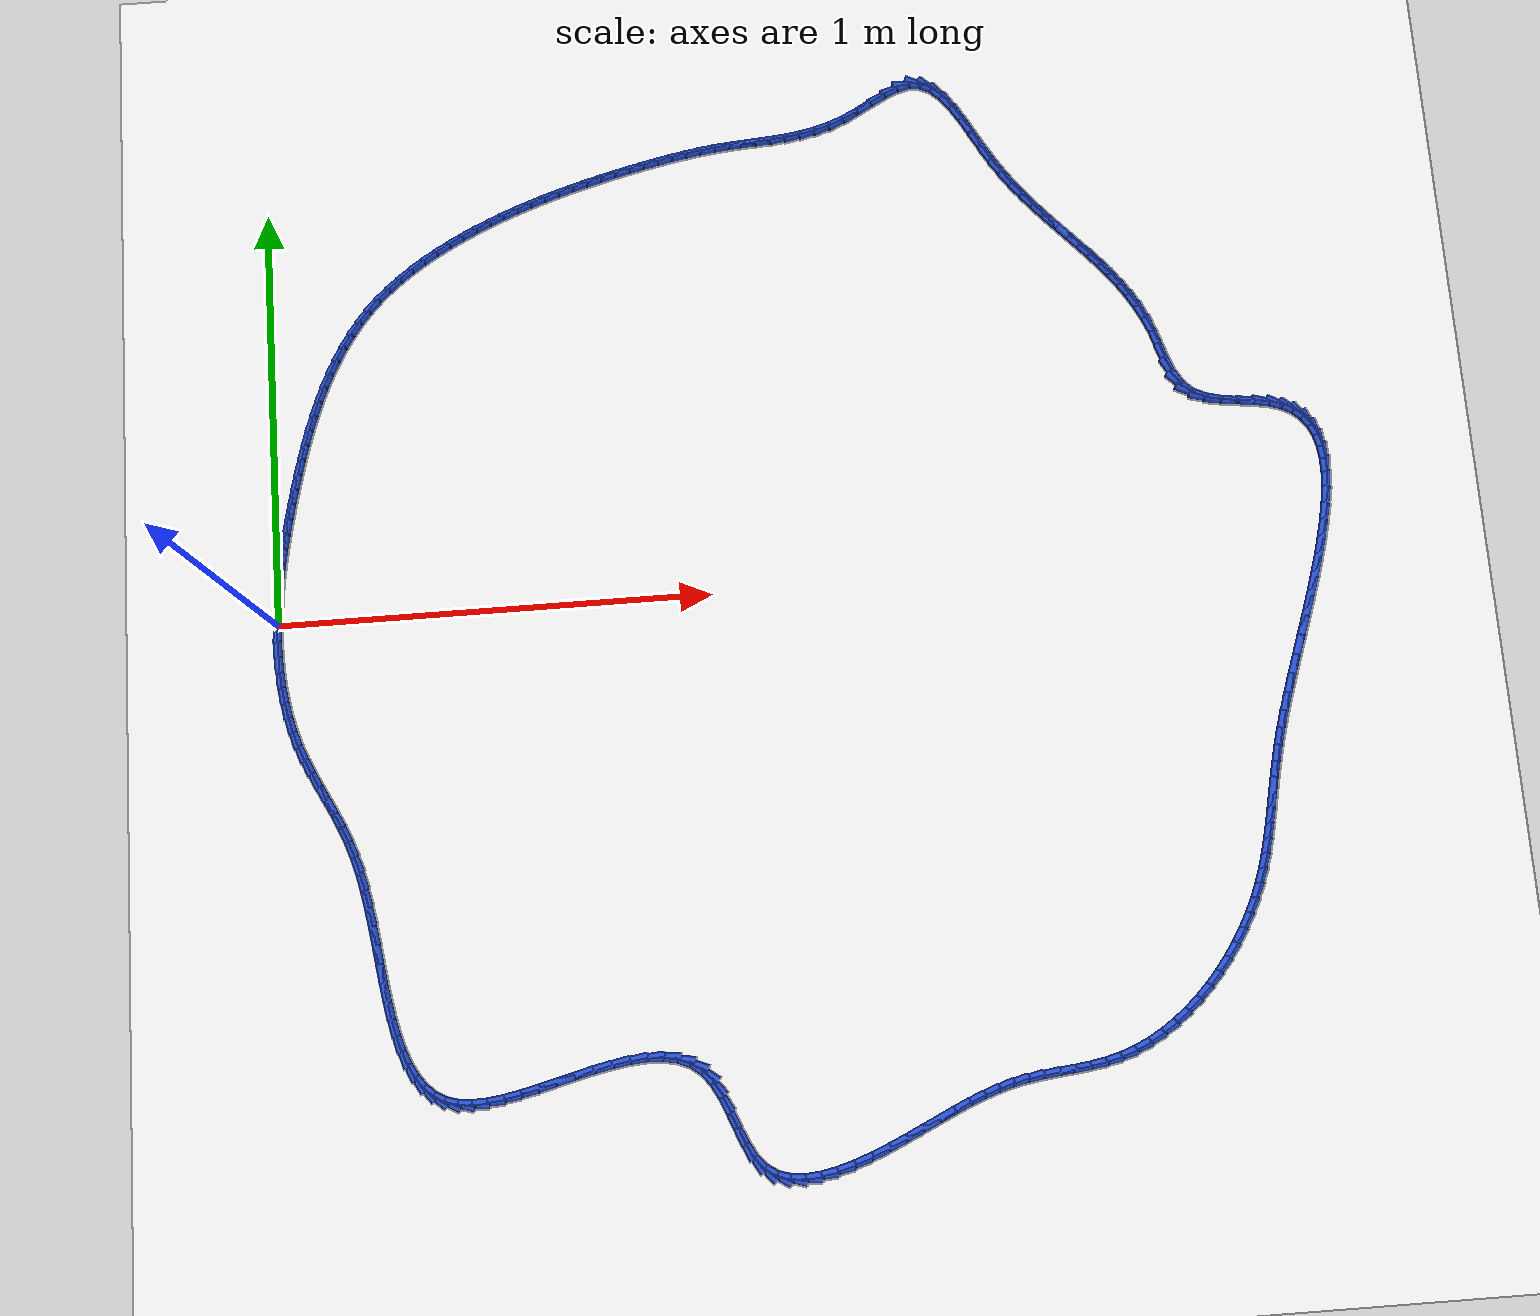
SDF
<sdf version="1.6">
 <world name="default">
  <light name="sun" type="directional">
   <pose>0 0 10 0 -0 0</pose>
   <diffuse>0.8 0.8 0.8 1</diffuse>
   <specular>0.2 0.2 0.2 1</specular>
   <attenuation>
    <range>1000</range>
    <constant>0.9</constant>
    <linear>0.01</linear>
    <quadratic>0.001</quadratic>
   </attenuation>
   <direction>-0.5 0.1 -0.9</direction>
  </light>
  <model name="ground_plane">
   <static>1</static>
   <link name="link">
    <collision name="collision">
     <geometry><plane><normal>0 0 1</normal><size>100 100</size></plane></geometry>
     <surface><friction><ode><mu>100</mu><mu2>50</mu2></ode></friction></surface>
    </collision>
    <visual name="visual">
     <cast_shadows>0</cast_shadows>
     <geometry><plane><normal>0 0 1</normal><size>100 100</size></plane></geometry>
     <material>
      <script><uri>file://media/materials/scripts/gazebo.material</uri><name>Gazebo/WhiteGlow</name></script>
     </material>
    </visual>
   </link>
  </model>
  <gravity>0 0 -9.8</gravity>
  <magnetic_field>6e-06 2.3e-05 -4.2e-05</magnetic_field>
  <atmosphere type="adiabatic"/>
  <physics name="default_physics" default="0" type="ode">
   <max_step_size>0.001</max_step_size>
   <real_time_factor>1</real_time_factor>
   <real_time_update_rate>1000</real_time_update_rate>
  </physics>
  <scene><ambient>0.4 0.4 0.4 1</ambient><background>0.7 0.7 0.7 1</background><shadows>1</shadows></scene>
  <spherical_coordinates>
   <surface_model>EARTH_WGS84</surface_model>
   <latitude_deg>0</latitude_deg>
   <longitude_deg>0</longitude_deg>
   <elevation>0</elevation>
   <heading_deg>0</heading_deg>
  </spherical_coordinates>
  <model name="line">
   <link name="link_0">
    <pose>-4.336808689942018e-18 2.0816681711721685e-17 0.01 0 1.57 1.5228255407405091</pose>
    <collision name="collision">
     <geometry><cylinder><radius>0.01</radius><length>0.08</length></cylinder></geometry>
    </collision>
    <visual name="visual">
     <material>
      <script><name>Gazebo/Blue</name><uri>file://media/materials/scripts/gazebo.material</uri></script>
     </material>
     <geometry><cylinder><radius>0.01</radius><length>0.08</length></cylinder></geometry>
    </visual>
   </link>
   <link name="link_1">
    <pose>0.0017141860436077924 0.0357065432913914 0.01 0 1.57 1.4890325752673867</pose>
    <collision name="collision">
     <geometry><cylinder><radius>0.01</radius><length>0.08</length></cylinder></geometry>
    </collision>
    <visual name="visual">
     <material>
      <script><name>Gazebo/Blue</name><uri>file://media/materials/scripts/gazebo.material</uri></script>
     </material>
     <geometry><cylinder><radius>0.01</radius><length>0.08</length></cylinder></geometry>
    </visual>
   </link>
   <link name="link_2">
    <pose>0.004617474653295481 0.07113564083650696 0.01 0 1.57 1.4583774974147363</pose>
    <collision name="collision">
     <geometry><cylinder><radius>0.01</radius><length>0.08</length></cylinder></geometry>
    </collision>
    <visual name="visual">
     <material>
      <script><name>Gazebo/Blue</name><uri>file://media/materials/scripts/gazebo.material</uri></script>
     </material>
     <geometry><cylinder><radius>0.01</radius><length>0.08</length></cylinder></geometry>
    </visual>
   </link>
   <link name="link_3">
    <pose>0.008593571042337112 0.10635511716235745 0.01 0 1.57 1.4310927449233288</pose>
    <collision name="collision">
     <geometry><cylinder><radius>0.01</radius><length>0.08</length></cylinder></geometry>
    </collision>
    <visual name="visual">
     <material>
      <script><name>Gazebo/Blue</name><uri>file://media/materials/scripts/gazebo.material</uri></script>
     </material>
     <geometry><cylinder><radius>0.01</radius><length>0.08</length></cylinder></geometry>
    </visual>
   </link>
   <link name="link_4">
    <pose>0.013526180424006766 0.14143279679595372 0.01 0 1.57 1.407347139483378</pose>
    <collision name="collision">
     <geometry><cylinder><radius>0.01</radius><length>0.08</length></cylinder></geometry>
    </collision>
    <visual name="visual">
     <material>
      <script><name>Gazebo/Blue</name><uri>file://media/materials/scripts/gazebo.material</uri></script>
     </material>
     <geometry><cylinder><radius>0.01</radius><length>0.08</length></cylinder></geometry>
    </visual>
   </link>
   <link name="link_5">
    <pose>0.0192990080115785 0.17643650426430643 0.01 0 1.57 1.387251224445408</pose>
    <collision name="collision">
     <geometry><cylinder><radius>0.01</radius><length>0.08</length></cylinder></geometry>
    </collision>
    <visual name="visual">
     <material>
      <script><name>Gazebo/Blue</name><uri>file://media/materials/scripts/gazebo.material</uri></script>
     </material>
     <geometry><cylinder><radius>0.01</radius><length>0.08</length></cylinder></geometry>
    </visual>
   </link>
   <link name="link_6">
    <pose>0.025795759018326373 0.2114340640944264 0.01 0 1.57 1.3708642589614066</pose>
    <collision name="collision">
     <geometry><cylinder><radius>0.01</radius><length>0.08</length></cylinder></geometry>
    </collision>
    <visual name="visual">
     <material>
      <script><name>Gazebo/Blue</name><uri>file://media/materials/scripts/gazebo.material</uri></script>
     </material>
     <geometry><cylinder><radius>0.01</radius><length>0.08</length></cylinder></geometry>
    </visual>
   </link>
   <link name="link_7">
    <pose>0.032900138657524454 0.2464933008133243 0.01 0 1.57 1.3582017720819226</pose>
    <collision name="collision">
     <geometry><cylinder><radius>0.01</radius><length>0.08</length></cylinder></geometry>
    </collision>
    <visual name="visual">
     <material>
      <script><name>Gazebo/Blue</name><uri>file://media/materials/scripts/gazebo.material</uri></script>
     </material>
     <geometry><cylinder><radius>0.01</radius><length>0.08</length></cylinder></geometry>
    </visual>
   </link>
   <link name="link_8">
    <pose>0.0404958521424468 0.28168203894801097 0.01 0 1.57 1.3480790394034992</pose>
    <collision name="collision">
     <geometry><cylinder><radius>0.01</radius><length>0.08</length></cylinder></geometry>
    </collision>
    <visual name="visual">
     <material>
      <script><name>Gazebo/Blue</name><uri>file://media/materials/scripts/gazebo.material</uri></script>
     </material>
     <geometry><cylinder><radius>0.01</radius><length>0.08</length></cylinder></geometry>
    </visual>
   </link>
   <link name="link_9">
    <pose>0.04850288556423894 0.3170371867375543 0.01 0 1.57 1.3357887444665462</pose>
    <collision name="collision">
     <geometry><cylinder><radius>0.01</radius><length>0.08</length></cylinder></geometry>
    </collision>
    <visual name="visual">
     <material>
      <script><name>Gazebo/Blue</name><uri>file://media/materials/scripts/gazebo.material</uri></script>
     </material>
     <geometry><cylinder><radius>0.01</radius><length>0.08</length></cylinder></geometry>
    </visual>
   </link>
   <link name="link_10">
    <pose>0.05698697334673555 0.35247145483581954 0.01 0 1.57 1.3201157322766965</pose>
    <collision name="collision">
     <geometry><cylinder><radius>0.01</radius><length>0.08</length></cylinder></geometry>
    </collision>
    <visual name="visual">
     <material>
      <script><name>Gazebo/Blue</name><uri>file://media/materials/scripts/gazebo.material</uri></script>
     </material>
     <geometry><cylinder><radius>0.01</radius><length>0.08</length></cylinder></geometry>
    </visual>
   </link>
   <link name="link_11">
    <pose>0.06605044387418865 0.38786637081942593 0.01 0 1.57 1.3009800684974464</pose>
    <collision name="collision">
     <geometry><cylinder><radius>0.01</radius><length>0.08</length></cylinder></geometry>
    </collision>
    <visual name="visual">
     <material>
      <script><name>Gazebo/Blue</name><uri>file://media/materials/scripts/gazebo.material</uri></script>
     </material>
     <geometry><cylinder><radius>0.01</radius><length>0.08</length></cylinder></geometry>
    </visual>
   </link>
   <link name="link_12">
    <pose>0.07579562553095731 0.4231034622649014 0.01 0 1.57 1.2782644199969098</pose>
    <collision name="collision">
     <geometry><cylinder><radius>0.01</radius><length>0.08</length></cylinder></geometry>
    </collision>
    <visual name="visual">
     <material>
      <script><name>Gazebo/Blue</name><uri>file://media/materials/scripts/gazebo.material</uri></script>
     </material>
     <geometry><cylinder><radius>0.01</radius><length>0.08</length></cylinder></geometry>
    </visual>
   </link>
   <link name="link_13">
    <pose>0.08632484670140053 0.4580642567487738 0.01 0 1.57 1.2518191796785554</pose>
    <collision name="collision">
     <geometry><cylinder><radius>0.01</radius><length>0.08</length></cylinder></geometry>
    </collision>
    <visual name="visual">
     <material>
      <script><name>Gazebo/Blue</name><uri>file://media/materials/scripts/gazebo.material</uri></script>
     </material>
     <geometry><cylinder><radius>0.01</radius><length>0.08</length></cylinder></geometry>
    </visual>
   </link>
   <link name="link_14">
    <pose>0.09774043576987733 0.49263028184757096 0.01 0 1.57 1.221468965545286</pose>
    <collision name="collision">
     <geometry><cylinder><radius>0.01</radius><length>0.08</length></cylinder></geometry>
    </collision>
    <visual name="visual">
     <material>
      <script><name>Gazebo/Blue</name><uri>file://media/materials/scripts/gazebo.material</uri></script>
     </material>
     <geometry><cylinder><radius>0.01</radius><length>0.08</length></cylinder></geometry>
    </visual>
   </link>
   <link name="link_15">
    <pose>0.11014472112074677 0.526683065137821 0.01 0 1.57 1.1870214133615131</pose>
    <collision name="collision">
     <geometry><cylinder><radius>0.01</radius><length>0.08</length></cylinder></geometry>
    </collision>
    <visual name="visual">
     <material>
      <script><name>Gazebo/Blue</name><uri>file://media/materials/scripts/gazebo.material</uri></script>
     </material>
     <geometry><cylinder><radius>0.01</radius><length>0.08</length></cylinder></geometry>
    </visual>
   </link>
   <link name="link_16">
    <pose>0.12364003113836786 0.5601041341960513 0.01 0 1.57 1.1482793087308902</pose>
    <collision name="collision">
     <geometry><cylinder><radius>0.01</radius><length>0.08</length></cylinder></geometry>
    </collision>
    <visual name="visual">
     <material>
      <script><name>Gazebo/Blue</name><uri>file://media/materials/scripts/gazebo.material</uri></script>
     </material>
     <geometry><cylinder><radius>0.01</radius><length>0.08</length></cylinder></geometry>
    </visual>
   </link>
   <link name="link_17">
    <pose>0.13832869420709962 0.5927750165987903 0.01 0 1.57 1.105057148874962</pose>
    <collision name="collision">
     <geometry><cylinder><radius>0.01</radius><length>0.08</length></cylinder></geometry>
    </collision>
    <visual name="visual">
     <material>
      <script><name>Gazebo/Blue</name><uri>file://media/materials/scripts/gazebo.material</uri></script>
     </material>
     <geometry><cylinder><radius>0.01</radius><length>0.08</length></cylinder></geometry>
    </visual>
   </link>
   <link name="link_18">
    <pose>0.15431303871130114 0.6245772399225656 0.01 0 1.57 1.0572030738885174</pose>
    <collision name="collision">
     <geometry><cylinder><radius>0.01</radius><length>0.08</length></cylinder></geometry>
    </collision>
    <visual name="visual">
     <material>
      <script><name>Gazebo/Blue</name><uri>file://media/materials/scripts/gazebo.material</uri></script>
     </material>
     <geometry><cylinder><radius>0.01</radius><length>0.08</length></cylinder></geometry>
    </visual>
   </link>
   <link name="link_19">
    <pose>0.17169539303533127 0.655392331743905 0.01 0 1.57 1.0046266012586538</pose>
    <collision name="collision">
     <geometry><cylinder><radius>0.01</radius><length>0.08</length></cylinder></geometry>
    </collision>
    <visual name="visual">
     <material>
      <script><name>Gazebo/Blue</name><uri>file://media/materials/scripts/gazebo.material</uri></script>
     </material>
     <geometry><cylinder><radius>0.01</radius><length>0.08</length></cylinder></geometry>
    </visual>
   </link>
   <link name="link_20">
    <pose>0.1905780855635493 0.6851018196393366 0.01 0 1.57 0.9473315545258912</pose>
    <collision name="collision">
     <geometry><cylinder><radius>0.01</radius><length>0.08</length></cylinder></geometry>
    </collision>
    <visual name="visual">
     <material>
      <script><name>Gazebo/Blue</name><uri>file://media/materials/scripts/gazebo.material</uri></script>
     </material>
     <geometry><cylinder><radius>0.01</radius><length>0.08</length></cylinder></geometry>
    </visual>
   </link>
   <link name="link_21">
    <pose>0.21106344468031396 0.7135872311853879 0.01 0 1.57 0.8854522056791655</pose>
    <collision name="collision">
     <geometry><cylinder><radius>0.01</radius><length>0.08</length></cylinder></geometry>
    </collision>
    <visual name="visual">
     <material>
      <script><name>Gazebo/Blue</name><uri>file://media/materials/scripts/gazebo.material</uri></script>
     </material>
     <geometry><cylinder><radius>0.01</radius><length>0.08</length></cylinder></geometry>
    </visual>
   </link>
   <link name="link_22">
    <pose>0.2332537890926638 0.7407301003371942 0.01 0 1.57 0.8210329847435851</pose>
    <collision name="collision">
     <geometry><cylinder><radius>0.01</radius><length>0.08</length></cylinder></geometry>
    </collision>
    <visual name="visual">
     <material>
      <script><name>Gazebo/Blue</name><uri>file://media/materials/scripts/gazebo.material</uri></script>
     </material>
     <geometry><cylinder><radius>0.01</radius><length>0.08</length></cylinder></geometry>
    </visual>
   </link>
   <link name="link_23">
    <pose>0.25719946669421806 0.7664462165438233 0.01 0 1.57 0.7601839134821964</pose>
    <collision name="collision">
     <geometry><cylinder><radius>0.01</radius><length>0.08</length></cylinder></geometry>
    </collision>
    <visual name="visual">
     <material>
      <script><name>Gazebo/Blue</name><uri>file://media/materials/scripts/gazebo.material</uri></script>
     </material>
     <geometry><cylinder><radius>0.01</radius><length>0.08</length></cylinder></geometry>
    </visual>
   </link>
   <link name="link_24">
    <pose>0.28277735230433243 0.7907657104672643 0.01 0 1.57 0.7041427560756071</pose>
    <collision name="collision">
     <geometry><cylinder><radius>0.01</radius><length>0.08</length></cylinder></geometry>
    </collision>
    <visual name="visual">
     <material>
      <script><name>Gazebo/Blue</name><uri>file://media/materials/scripts/gazebo.material</uri></script>
     </material>
     <geometry><cylinder><radius>0.01</radius><length>0.08</length></cylinder></geometry>
    </visual>
   </link>
   <link name="link_25">
    <pose>0.3098281697414136 0.8137425409590655 0.01 0 1.57 0.6527942722596191</pose>
    <collision name="collision">
     <geometry><cylinder><radius>0.01</radius><length>0.08</length></cylinder></geometry>
    </collision>
    <visual name="visual">
     <material>
      <script><name>Gazebo/Blue</name><uri>file://media/materials/scripts/gazebo.material</uri></script>
     </material>
     <geometry><cylinder><radius>0.01</radius><length>0.08</length></cylinder></geometry>
    </visual>
   </link>
   <link name="link_26">
    <pose>0.33819264282386824 0.8354306668707755 0.01 0 1.57 0.6059396255281584</pose>
    <collision name="collision">
     <geometry><cylinder><radius>0.01</radius><length>0.08</length></cylinder></geometry>
    </collision>
    <visual name="visual">
     <material>
      <script><name>Gazebo/Blue</name><uri>file://media/materials/scripts/gazebo.material</uri></script>
     </material>
     <geometry><cylinder><radius>0.01</radius><length>0.08</length></cylinder></geometry>
    </visual>
   </link>
   <link name="link_27">
    <pose>0.36771149537010295 0.855884047053942 0.01 0 1.57 0.5633308143257734</pose>
    <collision name="collision">
     <geometry><cylinder><radius>0.01</radius><length>0.08</length></cylinder></geometry>
    </collision>
    <visual name="visual">
     <material>
      <script><name>Gazebo/Blue</name><uri>file://media/materials/scripts/gazebo.material</uri></script>
     </material>
     <geometry><cylinder><radius>0.01</radius><length>0.08</length></cylinder></geometry>
    </visual>
   </link>
   <link name="link_28">
    <pose>0.3982254511985245 0.8751566403601135 0.01 0 1.57 0.5246975988057454</pose>
    <collision name="collision">
     <geometry><cylinder><radius>0.01</radius><length>0.08</length></cylinder></geometry>
    </collision>
    <visual name="visual">
     <material>
      <script><name>Gazebo/Blue</name><uri>file://media/materials/scripts/gazebo.material</uri></script>
     </material>
     <geometry><cylinder><radius>0.01</radius><length>0.08</length></cylinder></geometry>
    </visual>
   </link>
   <link name="link_29">
    <pose>0.4295752341275396 0.8933024056408384 0.01 0 1.57 0.489767320861686</pose>
    <collision name="collision">
     <geometry><cylinder><radius>0.01</radius><length>0.08</length></cylinder></geometry>
    </collision>
    <visual name="visual">
     <material>
      <script><name>Gazebo/Blue</name><uri>file://media/materials/scripts/gazebo.material</uri></script>
     </material>
     <geometry><cylinder><radius>0.01</radius><length>0.08</length></cylinder></geometry>
    </visual>
   </link>
   <link name="link_30">
    <pose>0.461601567975555 0.9103753017476645 0.01 0 1.57 0.45827878508697806</pose>
    <collision name="collision">
     <geometry><cylinder><radius>0.01</radius><length>0.08</length></cylinder></geometry>
    </collision>
    <visual name="visual">
     <material>
      <script><name>Gazebo/Blue</name><uri>file://media/materials/scripts/gazebo.material</uri></script>
     </material>
     <geometry><cylinder><radius>0.01</radius><length>0.08</length></cylinder></geometry>
    </visual>
   </link>
   <link name="link_31">
    <pose>0.49414517656097723 0.92642928753214 0.01 0 1.57 0.4299916018830504</pose>
    <collision name="collision">
     <geometry><cylinder><radius>0.01</radius><length>0.08</length></cylinder></geometry>
    </collision>
    <visual name="visual">
     <material>
      <script><name>Gazebo/Blue</name><uri>file://media/materials/scripts/gazebo.material</uri></script>
     </material>
     <geometry><cylinder><radius>0.01</radius><length>0.08</length></cylinder></geometry>
    </visual>
   </link>
   <link name="link_32">
    <pose>0.527046783702213 0.9415183218458134 0.01 0 1.57 0.4045984454426594</pose>
    <collision name="collision">
     <geometry><cylinder><radius>0.01</radius><length>0.08</length></cylinder></geometry>
    </collision>
    <visual name="visual">
     <material>
      <script><name>Gazebo/Blue</name><uri>file://media/materials/scripts/gazebo.material</uri></script>
     </material>
     <geometry><cylinder><radius>0.01</radius><length>0.08</length></cylinder></geometry>
    </visual>
   </link>
   <link name="link_33">
    <pose>0.5601562460246211 0.9556965965973488 0.01 0 1.57 0.38100162012030997</pose>
    <collision name="collision">
     <geometry><cylinder><radius>0.01</radius><length>0.08</length></cylinder></geometry>
    </collision>
    <visual name="visual">
     <material>
      <script><name>Gazebo/Blue</name><uri>file://media/materials/scripts/gazebo.material</uri></script>
     </material>
     <geometry><cylinder><radius>0.01</radius><length>0.08</length></cylinder></geometry>
    </visual>
   </link>
   <link name="link_34">
    <pose>0.5934188185372113 0.9690207381355841 0.01 0 1.57 0.35867715312286735</pose>
    <collision name="collision">
     <geometry><cylinder><radius>0.01</radius><length>0.08</length></cylinder></geometry>
    </collision>
    <visual name="visual">
     <material>
      <script><name>Gazebo/Blue</name><uri>file://media/materials/scripts/gazebo.material</uri></script>
     </material>
     <geometry><cylinder><radius>0.01</radius><length>0.08</length></cylinder></geometry>
    </visual>
   </link>
   <link name="link_35">
    <pose>0.6268365475781638 0.9815488220487255 0.01 0 1.57 0.33769945399846885</pose>
    <collision name="collision">
     <geometry><cylinder><radius>0.01</radius><length>0.08</length></cylinder></geometry>
    </collision>
    <visual name="visual">
     <material>
      <script><name>Gazebo/Blue</name><uri>file://media/materials/scripts/gazebo.material</uri></script>
     </material>
     <geometry><cylinder><radius>0.01</radius><length>0.08</length></cylinder></geometry>
    </visual>
   </link>
   <link name="link_36">
    <pose>0.6604122335720984 0.9933389431682658 0.01 0 1.57 0.3181386986248441</pose>
    <collision name="collision">
     <geometry><cylinder><radius>0.01</radius><length>0.08</length></cylinder></geometry>
    </collision>
    <visual name="visual">
     <material>
      <script><name>Gazebo/Blue</name><uri>file://media/materials/scripts/gazebo.material</uri></script>
     </material>
     <geometry><cylinder><radius>0.01</radius><length>0.08</length></cylinder></geometry>
    </visual>
   </link>
   <link name="link_37">
    <pose>0.6941486769436354 1.0044491963256963 0.01 0 1.57 0.3000533269703848</pose>
    <collision name="collision">
     <geometry><cylinder><radius>0.01</radius><length>0.08</length></cylinder></geometry>
    </collision>
    <visual name="visual">
     <material>
      <script><name>Gazebo/Blue</name><uri>file://media/materials/scripts/gazebo.material</uri></script>
     </material>
     <geometry><cylinder><radius>0.01</radius><length>0.08</length></cylinder></geometry>
    </visual>
   </link>
   <link name="link_38">
    <pose>0.7280486781173943 1.0149376763525089 0.01 0 1.57 0.2834905531490338</pose>
    <collision name="collision">
     <geometry><cylinder><radius>0.01</radius><length>0.08</length></cylinder></geometry>
    </collision>
    <visual name="visual">
     <material>
      <script><name>Gazebo/Blue</name><uri>file://media/materials/scripts/gazebo.material</uri></script>
     </material>
     <geometry><cylinder><radius>0.01</radius><length>0.08</length></cylinder></geometry>
    </visual>
   </link>
   <link name="link_39">
    <pose>0.7621150375179948 1.0248624780801956 0.01 0 1.57 0.26848707169760744</pose>
    <collision name="collision">
     <geometry><cylinder><radius>0.01</radius><length>0.08</length></cylinder></geometry>
    </collision>
    <visual name="visual">
     <material>
      <script><name>Gazebo/Blue</name><uri>file://media/materials/scripts/gazebo.material</uri></script>
     </material>
     <geometry><cylinder><radius>0.01</radius><length>0.08</length></cylinder></geometry>
    </visual>
   </link>
   <link name="link_40">
    <pose>0.7963505555700576 1.034281696340249 0.01 0 1.57 0.2550698951712809</pose>
    <collision name="collision">
     <geometry><cylinder><radius>0.01</radius><length>0.08</length></cylinder></geometry>
    </collision>
    <visual name="visual">
     <material>
      <script><name>Gazebo/Blue</name><uri>file://media/materials/scripts/gazebo.material</uri></script>
     </material>
     <geometry><cylinder><radius>0.01</radius><length>0.08</length></cylinder></geometry>
    </visual>
   </link>
   <link name="link_41">
    <pose>0.8307580326982019 1.0432534259641604 0.01 0 1.57 0.2432552574607341</pose>
    <collision name="collision">
     <geometry><cylinder><radius>0.01</radius><length>0.08</length></cylinder></geometry>
    </collision>
    <visual name="visual">
     <material>
      <script><name>Gazebo/Blue</name><uri>file://media/materials/scripts/gazebo.material</uri></script>
     </material>
     <geometry><cylinder><radius>0.01</radius><length>0.08</length></cylinder></geometry>
    </visual>
   </link>
   <link name="link_42">
    <pose>0.8653402520343028 1.0518356838647942 0.01 0 1.57 0.23202307096497948</pose>
    <collision name="collision">
     <geometry><cylinder><radius>0.01</radius><length>0.08</length></cylinder></geometry>
    </collision>
    <visual name="visual">
     <material>
      <script><name>Gazebo/Blue</name><uri>file://media/materials/scripts/gazebo.material</uri></script>
     </material>
     <geometry><cylinder><radius>0.01</radius><length>0.08</length></cylinder></geometry>
    </visual>
   </link>
   <link name="link_43">
    <pose>0.9000911368951012 1.060046565899707 0.01 0 1.57 0.2186507471971308</pose>
    <collision name="collision">
     <geometry><cylinder><radius>0.01</radius><length>0.08</length></cylinder></geometry>
    </collision>
    <visual name="visual">
     <material>
      <script><name>Gazebo/Blue</name><uri>file://media/materials/scripts/gazebo.material</uri></script>
     </material>
     <geometry><cylinder><radius>0.01</radius><length>0.08</length></cylinder></geometry>
    </visual>
   </link>
   <link name="link_44">
    <pose>0.9349813316201964 1.0677992761967794 0.01 0 1.57 0.20265007443832417</pose>
    <collision name="collision">
     <geometry><cylinder><radius>0.01</radius><length>0.08</length></cylinder></geometry>
    </collision>
    <visual name="visual">
     <material>
      <script><name>Gazebo/Blue</name><uri>file://media/materials/scripts/gazebo.material</uri></script>
     </material>
     <geometry><cylinder><radius>0.01</radius><length>0.08</length></cylinder></geometry>
    </visual>
   </link>
   <link name="link_45">
    <pose>0.9699777030324707 1.0749899979357715 0.01 0 1.57 0.18395376565996616</pose>
    <collision name="collision">
     <geometry><cylinder><radius>0.01</radius><length>0.08</length></cylinder></geometry>
    </collision>
    <visual name="visual">
     <material>
      <script><name>Gazebo/Blue</name><uri>file://media/materials/scripts/gazebo.material</uri></script>
     </material>
     <geometry><cylinder><radius>0.01</radius><length>0.08</length></cylinder></geometry>
    </visual>
   </link>
   <link name="link_46">
    <pose>1.0050471179548073 1.0815149142964438 0.01 0 1.57 0.16247987473973194</pose>
    <collision name="collision">
     <geometry><cylinder><radius>0.01</radius><length>0.08</length></cylinder></geometry>
    </collision>
    <visual name="visual">
     <material>
      <script><name>Gazebo/Blue</name><uri>file://media/materials/scripts/gazebo.material</uri></script>
     </material>
     <geometry><cylinder><radius>0.01</radius><length>0.08</length></cylinder></geometry>
    </visual>
   </link>
   <link name="link_47">
    <pose>1.0401564432100892 1.0872702084585555 0.01 0 1.57 0.13813505867766</pose>
    <collision name="collision">
     <geometry><cylinder><radius>0.01</radius><length>0.08</length></cylinder></geometry>
    </collision>
    <visual name="visual">
     <material>
      <script><name>Gazebo/Blue</name><uri>file://media/materials/scripts/gazebo.material</uri></script>
     </material>
     <geometry><cylinder><radius>0.01</radius><length>0.08</length></cylinder></geometry>
    </visual>
   </link>
   <link name="link_48">
    <pose>1.075272545621199 1.0921520636018667 0.01 0 1.57 0.11081909394043994</pose>
    <collision name="collision">
     <geometry><cylinder><radius>0.01</radius><length>0.08</length></cylinder></geometry>
    </collision>
    <visual name="visual">
     <material>
      <script><name>Gazebo/Blue</name><uri>file://media/materials/scripts/gazebo.material</uri></script>
     </material>
     <geometry><cylinder><radius>0.01</radius><length>0.08</length></cylinder></geometry>
    </visual>
   </link>
   <link name="link_49">
    <pose>1.1103622927940897 1.096056674701157 0.01 0 1.57 0.08438259437875097</pose>
    <collision name="collision">
     <geometry><cylinder><radius>0.01</radius><length>0.08</length></cylinder></geometry>
    </collision>
    <visual name="visual">
     <material>
      <script><name>Gazebo/Blue</name><uri>file://media/materials/scripts/gazebo.material</uri></script>
     </material>
     <geometry><cylinder><radius>0.01</radius><length>0.08</length></cylinder></geometry>
    </visual>
   </link>
   <link name="link_50">
    <pose>1.1454018605543699 1.0990204421012482 0.01 0 1.57 0.07268358910765241</pose>
    <collision name="collision">
     <geometry><cylinder><radius>0.01</radius><length>0.08</length></cylinder></geometry>
    </collision>
    <visual name="visual">
     <material>
      <script><name>Gazebo/Blue</name><uri>file://media/materials/scripts/gazebo.material</uri></script>
     </material>
     <geometry><cylinder><radius>0.01</radius><length>0.08</length></cylinder></geometry>
    </visual>
   </link>
   <link name="link_51">
    <pose>1.1803998858705436 1.1015687131981093 0.01 0 1.57 0.07888852824627425</pose>
    <collision name="collision">
     <geometry><cylinder><radius>0.01</radius><length>0.08</length></cylinder></geometry>
    </collision>
    <visual name="visual">
     <material>
      <script><name>Gazebo/Blue</name><uri>file://media/materials/scripts/gazebo.material</uri></script>
     </material>
     <geometry><cylinder><radius>0.01</radius><length>0.08</length></cylinder></geometry>
    </visual>
   </link>
   <link name="link_52">
    <pose>1.2153720775680694 1.104333355469699 0.01 0 1.57 0.10297167423270662</pose>
    <collision name="collision">
     <geometry><cylinder><radius>0.01</radius><length>0.08</length></cylinder></geometry>
    </collision>
    <visual name="visual">
     <material>
      <script><name>Gazebo/Blue</name><uri>file://media/materials/scripts/gazebo.material</uri></script>
     </material>
     <geometry><cylinder><radius>0.01</radius><length>0.08</length></cylinder></geometry>
    </visual>
   </link>
   <link name="link_53">
    <pose>1.2503341444724028 1.1079462363939747 0.01 0 1.57 0.14463154132239064</pose>
    <collision name="collision">
     <geometry><cylinder><radius>0.01</radius><length>0.08</length></cylinder></geometry>
    </collision>
    <visual name="visual">
     <material>
      <script><name>Gazebo/Blue</name><uri>file://media/materials/scripts/gazebo.material</uri></script>
     </material>
     <geometry><cylinder><radius>0.01</radius><length>0.08</length></cylinder></geometry>
    </visual>
   </link>
   <link name="link_54">
    <pose>1.2853017954090014 1.1130392234488942 0.01 0 1.57 0.20308235742694217</pose>
    <collision name="collision">
     <geometry><cylinder><radius>0.01</radius><length>0.08</length></cylinder></geometry>
    </collision>
    <visual name="visual">
     <material>
      <script><name>Gazebo/Blue</name><uri>file://media/materials/scripts/gazebo.material</uri></script>
     </material>
     <geometry><cylinder><radius>0.01</radius><length>0.08</length></cylinder></geometry>
    </visual>
   </link>
   <link name="link_55">
    <pose>1.3202907392033232 1.1202441841124158 0.01 0 1.57 0.2767519014179109</pose>
    <collision name="collision">
     <geometry><cylinder><radius>0.01</radius><length>0.08</length></cylinder></geometry>
    </collision>
    <visual name="visual">
     <material>
      <script><name>Gazebo/Blue</name><uri>file://media/materials/scripts/gazebo.material</uri></script>
     </material>
     <geometry><cylinder><radius>0.01</radius><length>0.08</length></cylinder></geometry>
    </visual>
   </link>
   <link name="link_56">
    <pose>1.355316684680824 1.1301929858624973 0.01 0 1.57 0.3630130115371787</pose>
    <collision name="collision">
     <geometry><cylinder><radius>0.01</radius><length>0.08</length></cylinder></geometry>
    </collision>
    <visual name="visual">
     <material>
      <script><name>Gazebo/Blue</name><uri>file://media/materials/scripts/gazebo.material</uri></script>
     </material>
     <geometry><cylinder><radius>0.01</radius><length>0.08</length></cylinder></geometry>
    </visual>
   </link>
   <link name="link_57">
    <pose>1.3903953406669616 1.143517496177096 0.01 0 1.57 0.45421878053178943</pose>
    <collision name="collision">
     <geometry><cylinder><radius>0.01</radius><length>0.08</length></cylinder></geometry>
    </collision>
    <visual name="visual">
     <material>
      <script><name>Gazebo/Blue</name><uri>file://media/materials/scripts/gazebo.material</uri></script>
     </material>
     <geometry><cylinder><radius>0.01</radius><length>0.08</length></cylinder></geometry>
    </visual>
   </link>
   <link name="link_58">
    <pose>1.425513417673205 1.1606645617772307 0.01 0 1.57 0.506772204871337</pose>
    <collision name="collision">
     <geometry><cylinder><radius>0.01</radius><length>0.08</length></cylinder></geometry>
    </collision>
    <visual name="visual">
     <material>
      <script><name>Gazebo/Blue</name><uri>file://media/materials/scripts/gazebo.material</uri></script>
     </material>
     <geometry><cylinder><radius>0.01</radius><length>0.08</length></cylinder></geometry>
    </visual>
   </link>
   <link name="link_59">
    <pose>1.4603302745162976 1.1799923955975342 0.01 0 1.57 0.4998025724112969</pose>
    <collision name="collision">
     <geometry><cylinder><radius>0.01</radius><length>0.08</length></cylinder></geometry>
    </collision>
    <visual name="visual">
     <material>
      <script><name>Gazebo/Blue</name><uri>file://media/materials/scripts/gazebo.material</uri></script>
     </material>
     <geometry><cylinder><radius>0.01</radius><length>0.08</length></cylinder></geometry>
    </visual>
   </link>
   <link name="link_60">
    <pose>1.4942986164098497 1.198540678533446 0.01 0 1.57 0.42620709518799016</pose>
    <collision name="collision">
     <geometry><cylinder><radius>0.01</radius><length>0.08</length></cylinder></geometry>
    </collision>
    <visual name="visual">
     <material>
      <script><name>Gazebo/Blue</name><uri>file://media/materials/scripts/gazebo.material</uri></script>
     </material>
     <geometry><cylinder><radius>0.01</radius><length>0.08</length></cylinder></geometry>
    </visual>
   </link>
   <link name="link_61">
    <pose>1.526867902729303 1.2133283817441345 0.01 0 1.57 0.2569657556382772</pose>
    <collision name="collision">
     <geometry><cylinder><radius>0.01</radius><length>0.08</length></cylinder></geometry>
    </collision>
    <visual name="visual">
     <material>
      <script><name>Gazebo/Blue</name><uri>file://media/materials/scripts/gazebo.material</uri></script>
     </material>
     <geometry><cylinder><radius>0.01</radius><length>0.08</length></cylinder></geometry>
    </visual>
   </link>
   <link name="link_62">
    <pose>1.5574875928500997 1.221374476388768 0.01 0 1.57 -0.05772509660578937</pose>
    <collision name="collision">
     <geometry><cylinder><radius>0.01</radius><length>0.08</length></cylinder></geometry>
    </collision>
    <visual name="visual">
     <material>
      <script><name>Gazebo/Blue</name><uri>file://media/materials/scripts/gazebo.material</uri></script>
     </material>
     <geometry><cylinder><radius>0.01</radius><length>0.08</length></cylinder></geometry>
    </visual>
   </link>
   <link name="link_63">
    <pose>1.58561835256482 1.2197488195012647 0.01 0 1.57 -0.44578839142600923</pose>
    <collision name="collision">
     <geometry><cylinder><radius>0.01</radius><length>0.08</length></cylinder></geometry>
    </collision>
    <visual name="visual">
     <material>
      <script><name>Gazebo/Blue</name><uri>file://media/materials/scripts/gazebo.material</uri></script>
     </material>
     <geometry><cylinder><radius>0.01</radius><length>0.08</length></cylinder></geometry>
    </visual>
   </link>
   <link name="link_64">
    <pose>1.6111655470808754 1.2075405503216563 0.01 0 1.57 -0.7315847116976266</pose>
    <collision name="collision">
     <geometry><cylinder><radius>0.01</radius><length>0.08</length></cylinder></geometry>
    </collision>
    <visual name="visual">
     <material>
      <script><name>Gazebo/Blue</name><uri>file://media/materials/scripts/gazebo.material</uri></script>
     </material>
     <geometry><cylinder><radius>0.01</radius><length>0.08</length></cylinder></geometry>
    </visual>
   </link>
   <link name="link_65">
    <pose>1.6346175126297373 1.1864859512530002 0.01 0 1.57 -0.90712623595277</pose>
    <collision name="collision">
     <geometry><cylinder><radius>0.01</radius><length>0.08</length></cylinder></geometry>
    </collision>
    <visual name="visual">
     <material>
      <script><name>Gazebo/Blue</name><uri>file://media/materials/scripts/gazebo.material</uri></script>
     </material>
     <geometry><cylinder><radius>0.01</radius><length>0.08</length></cylinder></geometry>
    </visual>
   </link>
   <link name="link_66">
    <pose>1.6565020831741193 1.158500655206174 0.01 0 1.57 -1.0074220827951799</pose>
    <collision name="collision">
     <geometry><cylinder><radius>0.01</radius><length>0.08</length></cylinder></geometry>
    </collision>
    <visual name="visual">
     <material>
      <script><name>Gazebo/Blue</name><uri>file://media/materials/scripts/gazebo.material</uri></script>
     </material>
     <geometry><cylinder><radius>0.01</radius><length>0.08</length></cylinder></geometry>
    </visual>
   </link>
   <link name="link_67">
    <pose>1.6773470926767335 1.125500295092055 0.01 0 1.57 -1.0578357391321325</pose>
    <collision name="collision">
     <geometry><cylinder><radius>0.01</radius><length>0.08</length></cylinder></geometry>
    </collision>
    <visual name="visual">
     <material>
      <script><name>Gazebo/Blue</name><uri>file://media/materials/scripts/gazebo.material</uri></script>
     </material>
     <geometry><cylinder><radius>0.01</radius><length>0.08</length></cylinder></geometry>
    </visual>
   </link>
   <link name="link_68">
    <pose>1.6976803751002927 1.0894005038215189 0.01 0 1.57 -1.0711832746636416</pose>
    <collision name="collision">
     <geometry><cylinder><radius>0.01</radius><length>0.08</length></cylinder></geometry>
    </collision>
    <visual name="visual">
     <material>
      <script><name>Gazebo/Blue</name><uri>file://media/materials/scripts/gazebo.material</uri></script>
     </material>
     <geometry><cylinder><radius>0.01</radius><length>0.08</length></cylinder></geometry>
    </visual>
   </link>
   <link name="link_69">
    <pose>1.718029764407509 1.0521169143054432 0.01 0 1.57 -1.0515163306645523</pose>
    <collision name="collision">
     <geometry><cylinder><radius>0.01</radius><length>0.08</length></cylinder></geometry>
    </collision>
    <visual name="visual">
     <material>
      <script><name>Gazebo/Blue</name><uri>file://media/materials/scripts/gazebo.material</uri></script>
     </material>
     <geometry><cylinder><radius>0.01</radius><length>0.08</length></cylinder></geometry>
    </visual>
   </link>
   <link name="link_70">
    <pose>1.7389230505974098 1.0155650245684458 0.01 0 1.57 -1.0050591435824352</pose>
    <collision name="collision">
     <geometry><cylinder><radius>0.01</radius><length>0.08</length></cylinder></geometry>
    </collision>
    <visual name="visual">
     <material>
      <script><name>Gazebo/Blue</name><uri>file://media/materials/scripts/gazebo.material</uri></script>
     </material>
     <geometry><cylinder><radius>0.01</radius><length>0.08</length></cylinder></geometry>
    </visual>
   </link>
   <link name="link_71">
    <pose>1.7607399707554683 0.9812060872059963 0.01 0 1.57 -0.957552552143876</pose>
    <collision name="collision">
     <geometry><cylinder><radius>0.01</radius><length>0.08</length></cylinder></geometry>
    </collision>
    <visual name="visual">
     <material>
      <script><name>Gazebo/Blue</name><uri>file://media/materials/scripts/gazebo.material</uri></script>
     </material>
     <geometry><cylinder><radius>0.01</radius><length>0.08</length></cylinder></geometry>
    </visual>
   </link>
   <link name="link_72">
    <pose>1.7833817943133627 0.9490333543567293 0.01 0 1.57 -0.915680178903412</pose>
    <collision name="collision">
     <geometry><cylinder><radius>0.01</radius><length>0.08</length></cylinder></geometry>
    </collision>
    <visual name="visual">
     <material>
      <script><name>Gazebo/Blue</name><uri>file://media/materials/scripts/gazebo.material</uri></script>
     </material>
     <geometry><cylinder><radius>0.01</radius><length>0.08</length></cylinder></geometry>
    </visual>
   </link>
   <link name="link_73">
    <pose>1.8066533141481878 0.9187440756498522 0.01 0 1.57 -0.8805521878444985</pose>
    <collision name="collision">
     <geometry><cylinder><radius>0.01</radius><length>0.08</length></cylinder></geometry>
    </collision>
    <visual name="visual">
     <material>
      <script><name>Gazebo/Blue</name><uri>file://media/materials/scripts/gazebo.material</uri></script>
     </material>
     <geometry><cylinder><radius>0.01</radius><length>0.08</length></cylinder></geometry>
    </visual>
   </link>
   <link name="link_74">
    <pose>1.8303593231370383 0.890035500714571 0.01 0 1.57 -0.8531341565264051</pose>
    <collision name="collision">
     <geometry><cylinder><radius>0.01</radius><length>0.08</length></cylinder></geometry>
    </collision>
    <visual name="visual">
     <material>
      <script><name>Gazebo/Blue</name><uri>file://media/materials/scripts/gazebo.material</uri></script>
     </material>
     <geometry><cylinder><radius>0.01</radius><length>0.08</length></cylinder></geometry>
    </visual>
   </link>
   <link name="link_75">
    <pose>1.8543046141570092 0.8626048791800941 0.01 0 1.57 -0.834245450800011</pose>
    <collision name="collision">
     <geometry><cylinder><radius>0.01</radius><length>0.08</length></cylinder></geometry>
    </collision>
    <visual name="visual">
     <material>
      <script><name>Gazebo/Blue</name><uri>file://media/materials/scripts/gazebo.material</uri></script>
     </material>
     <geometry><cylinder><radius>0.01</radius><length>0.08</length></cylinder></geometry>
    </visual>
   </link>
   <link name="link_76">
    <pose>1.8782939800851945 0.8361494606756272 0.01 0 1.57 -0.8245696743021435</pose>
    <collision name="collision">
     <geometry><cylinder><radius>0.01</radius><length>0.08</length></cylinder></geometry>
    </collision>
    <visual name="visual">
     <material>
      <script><name>Gazebo/Blue</name><uri>file://media/materials/scripts/gazebo.material</uri></script>
     </material>
     <geometry><cylinder><radius>0.01</radius><length>0.08</length></cylinder></geometry>
    </visual>
   </link>
   <link name="link_77">
    <pose>1.9021322137986894 0.810366494830378 0.01 0 1.57 -0.824665627592376</pose>
    <collision name="collision">
     <geometry><cylinder><radius>0.01</radius><length>0.08</length></cylinder></geometry>
    </collision>
    <visual name="visual">
     <material>
      <script><name>Gazebo/Blue</name><uri>file://media/materials/scripts/gazebo.material</uri></script>
     </material>
     <geometry><cylinder><radius>0.01</radius><length>0.08</length></cylinder></geometry>
    </visual>
   </link>
   <link name="link_78">
    <pose>1.9256241081745888 0.7849532312735531 0.01 0 1.57 -0.8349668310422012</pose>
    <collision name="collision">
     <geometry><cylinder><radius>0.01</radius><length>0.08</length></cylinder></geometry>
    </collision>
    <visual name="visual">
     <material>
      <script><name>Gazebo/Blue</name><uri>file://media/materials/scripts/gazebo.material</uri></script>
     </material>
     <geometry><cylinder><radius>0.01</radius><length>0.08</length></cylinder></geometry>
    </visual>
   </link>
   <link name="link_79">
    <pose>1.9485744560899874 0.75960691963436 0.01 0 1.57 -0.8557591959741188</pose>
    <collision name="collision">
     <geometry><cylinder><radius>0.01</radius><length>0.08</length></cylinder></geometry>
    </collision>
    <visual name="visual">
     <material>
      <script><name>Gazebo/Blue</name><uri>file://media/materials/scripts/gazebo.material</uri></script>
     </material>
     <geometry><cylinder><radius>0.01</radius><length>0.08</length></cylinder></geometry>
    </visual>
   </link>
   <link name="link_80">
    <pose>1.9707880504219792 0.734024809542005 0.01 0 1.57 -0.8871299552987736</pose>
    <collision name="collision">
     <geometry><cylinder><radius>0.01</radius><length>0.08</length></cylinder></geometry>
    </collision>
    <visual name="visual">
     <material>
      <script><name>Gazebo/Blue</name><uri>file://media/materials/scripts/gazebo.material</uri></script>
     </material>
     <geometry><cylinder><radius>0.01</radius><length>0.08</length></cylinder></geometry>
    </visual>
   </link>
   <link name="link_81">
    <pose>1.9920696840476593 0.7079041506256956 0.01 0 1.57 -0.9288875711741507</pose>
    <collision name="collision">
     <geometry><cylinder><radius>0.01</radius><length>0.08</length></cylinder></geometry>
    </collision>
    <visual name="visual">
     <material>
      <script><name>Gazebo/Blue</name><uri>file://media/materials/scripts/gazebo.material</uri></script>
     </material>
     <geometry><cylinder><radius>0.01</radius><length>0.08</length></cylinder></geometry>
    </visual>
   </link>
   <link name="link_82">
    <pose>2.012224149844122 0.6809421925146384 0.01 0 1.57 -0.9804634106747375</pose>
    <collision name="collision">
     <geometry><cylinder><radius>0.01</radius><length>0.08</length></cylinder></geometry>
    </collision>
    <visual name="visual">
     <material>
      <script><name>Gazebo/Blue</name><uri>file://media/materials/scripts/gazebo.material</uri></script>
     </material>
     <geometry><cylinder><radius>0.01</radius><length>0.08</length></cylinder></geometry>
    </visual>
   </link>
   <link name="link_83">
    <pose>2.031056240688463 0.6528361848380404 0.01 0 1.57 -1.0408211136673151</pose>
    <collision name="collision">
     <geometry><cylinder><radius>0.01</radius><length>0.08</length></cylinder></geometry>
    </collision>
    <visual name="visual">
     <material>
      <script><name>Gazebo/Blue</name><uri>file://media/materials/scripts/gazebo.material</uri></script>
     </material>
     <geometry><cylinder><radius>0.01</radius><length>0.08</length></cylinder></geometry>
    </visual>
   </link>
   <link name="link_84">
    <pose>2.048370749457776 0.6232833772251092 0.01 0 1.57 -1.1084135590315929</pose>
    <collision name="collision">
     <geometry><cylinder><radius>0.01</radius><length>0.08</length></cylinder></geometry>
    </collision>
    <visual name="visual">
     <material>
      <script><name>Gazebo/Blue</name><uri>file://media/materials/scripts/gazebo.material</uri></script>
     </material>
     <geometry><cylinder><radius>0.01</radius><length>0.08</length></cylinder></geometry>
    </visual>
   </link>
   <link name="link_85">
    <pose>2.0639724690291565 0.5919810193050509 0.01 0 1.57 -1.1812291533747508</pose>
    <collision name="collision">
     <geometry><cylinder><radius>0.01</radius><length>0.08</length></cylinder></geometry>
    </collision>
    <visual name="visual">
     <material>
      <script><name>Gazebo/Blue</name><uri>file://media/materials/scripts/gazebo.material</uri></script>
     </material>
     <geometry><cylinder><radius>0.01</radius><length>0.08</length></cylinder></geometry>
    </visual>
   </link>
   <link name="link_86">
    <pose>2.0776661922796986 0.558626360707073 0.01 0 1.57 -1.2527177371258107</pose>
    <collision name="collision">
     <geometry><cylinder><radius>0.01</radius><length>0.08</length></cylinder></geometry>
    </collision>
    <visual name="visual">
     <material>
      <script><name>Gazebo/Blue</name><uri>file://media/materials/scripts/gazebo.material</uri></script>
     </material>
     <geometry><cylinder><radius>0.01</radius><length>0.08</length></cylinder></geometry>
    </visual>
   </link>
   <link name="link_87">
    <pose>2.0893780192867184 0.5230560333537888 0.01 0 1.57 -1.2729560645764586</pose>
    <collision name="collision">
     <geometry><cylinder><radius>0.01</radius><length>0.08</length></cylinder></geometry>
    </collision>
    <visual name="visual">
     <material>
      <script><name>Gazebo/Blue</name><uri>file://media/materials/scripts/gazebo.material</uri></script>
     </material>
     <geometry><cylinder><radius>0.01</radius><length>0.08</length></cylinder></geometry>
    </visual>
   </link>
   <link name="link_88">
    <pose>2.100507638792732 0.48679982643563313 0.01 0 1.57 -1.2101813102977534</pose>
    <collision name="collision">
     <geometry><cylinder><radius>0.01</radius><length>0.08</length></cylinder></geometry>
    </collision>
    <visual name="visual">
     <material>
      <script><name>Gazebo/Blue</name><uri>file://media/materials/scripts/gazebo.material</uri></script>
     </material>
     <geometry><cylinder><radius>0.01</radius><length>0.08</length></cylinder></geometry>
    </visual>
   </link>
   <link name="link_89">
    <pose>2.113436435325002 0.4525155001922085 0.01 0 1.57 -1.046746015834272</pose>
    <collision name="collision">
     <geometry><cylinder><radius>0.01</radius><length>0.08</length></cylinder></geometry>
    </collision>
    <visual name="visual">
     <material>
      <script><name>Gazebo/Blue</name><uri>file://media/materials/scripts/gazebo.material</uri></script>
     </material>
     <geometry><cylinder><radius>0.01</radius><length>0.08</length></cylinder></geometry>
    </visual>
   </link>
   <link name="link_90">
    <pose>2.1305636055620076 0.42288128107191014 0.01 0 1.57 -0.7567599233735361</pose>
    <collision name="collision">
     <geometry><cylinder><radius>0.01</radius><length>0.08</length></cylinder></geometry>
    </collision>
    <visual name="visual">
     <material>
      <script><name>Gazebo/Blue</name><uri>file://media/materials/scripts/gazebo.material</uri></script>
     </material>
     <geometry><cylinder><radius>0.01</radius><length>0.08</length></cylinder></geometry>
    </visual>
   </link>
   <link name="link_91">
    <pose>2.1542394479452 0.4005241038728059 0.01 0 1.57 -0.4426309344426976</pose>
    <collision name="collision">
     <geometry><cylinder><radius>0.01</radius><length>0.08</length></cylinder></geometry>
    </collision>
    <visual name="visual">
     <material>
      <script><name>Gazebo/Blue</name><uri>file://media/materials/scripts/gazebo.material</uri></script>
     </material>
     <geometry><cylinder><radius>0.01</radius><length>0.08</length></cylinder></geometry>
    </visual>
   </link>
   <link name="link_92">
    <pose>2.184852789411084 0.38601342409188905 0.01 0 1.57 -0.24406776833048593</pose>
    <collision name="collision">
     <geometry><cylinder><radius>0.01</radius><length>0.08</length></cylinder></geometry>
    </collision>
    <visual name="visual">
     <material>
      <script><name>Gazebo/Blue</name><uri>file://media/materials/scripts/gazebo.material</uri></script>
     </material>
     <geometry><cylinder><radius>0.01</radius><length>0.08</length></cylinder></geometry>
    </visual>
   </link>
   <link name="link_93">
    <pose>2.2202088412823087 0.37720862183935344 0.01 0 1.57 -0.14280089788089562</pose>
    <collision name="collision">
     <geometry><cylinder><radius>0.01</radius><length>0.08</length></cylinder></geometry>
    </collision>
    <visual name="visual">
     <material>
      <script><name>Gazebo/Blue</name><uri>file://media/materials/scripts/gazebo.material</uri></script>
     </material>
     <geometry><cylinder><radius>0.01</radius><length>0.08</length></cylinder></geometry>
    </visual>
   </link>
   <link name="link_94">
    <pose>2.257936519876932 0.3717841531406344 0.01 0 1.57 -0.11530615651037719</pose>
    <collision name="collision">
     <geometry><cylinder><radius>0.01</radius><length>0.08</length></cylinder></geometry>
    </collision>
    <visual name="visual">
     <material>
      <script><name>Gazebo/Blue</name><uri>file://media/materials/scripts/gazebo.material</uri></script>
     </material>
     <geometry><cylinder><radius>0.01</radius><length>0.08</length></cylinder></geometry>
    </visual>
   </link>
   <link name="link_95">
    <pose>2.2956647415130105 0.36741447402116684 0.01 0 1.57 -0.15819206931085225</pose>
    <collision name="collision">
     <geometry><cylinder><radius>0.01</radius><length>0.08</length></cylinder></geometry>
    </collision>
    <visual name="visual">
     <material>
      <script><name>Gazebo/Blue</name><uri>file://media/materials/scripts/gazebo.material</uri></script>
     </material>
     <geometry><cylinder><radius>0.01</radius><length>0.08</length></cylinder></geometry>
    </visual>
   </link>
   <link name="link_96">
    <pose>2.3310224225085987 0.361774040506386 0.01 0 1.57 -0.28894721813249935</pose>
    <collision name="collision">
     <geometry><cylinder><radius>0.01</radius><length>0.08</length></cylinder></geometry>
    </collision>
    <visual name="visual">
     <material>
      <script><name>Gazebo/Blue</name><uri>file://media/materials/scripts/gazebo.material</uri></script>
     </material>
     <geometry><cylinder><radius>0.01</radius><length>0.08</length></cylinder></geometry>
    </visual>
   </link>
   <link name="link_97">
    <pose>2.361746143969743 0.3526409038600702 0.01 0 1.57 -0.48733417918766403</pose>
    <collision name="collision">
     <geometry><cylinder><radius>0.01</radius><length>0.08</length></cylinder></geometry>
    </collision>
    <visual name="visual">
     <material>
      <script><name>Gazebo/Blue</name><uri>file://media/materials/scripts/gazebo.material</uri></script>
     </material>
     <geometry><cylinder><radius>0.01</radius><length>0.08</length></cylinder></geometry>
    </visual>
   </link>
   <link name="link_98">
    <pose>2.3870606356461144 0.339225014449768 0.01 0 1.57 -0.7119260344662285</pose>
    <collision name="collision">
     <geometry><cylinder><radius>0.01</radius><length>0.08</length></cylinder></geometry>
    </collision>
    <visual name="visual">
     <material>
      <script><name>Gazebo/Blue</name><uri>file://media/materials/scripts/gazebo.material</uri></script>
     </material>
     <geometry><cylinder><radius>0.01</radius><length>0.08</length></cylinder></geometry>
    </visual>
   </link>
   <link name="link_99">
    <pose>2.4072764636870216 0.32178111623548 0.01 0 1.57 -0.9407965432231287</pose>
    <collision name="collision">
     <geometry><cylinder><radius>0.01</radius><length>0.08</length></cylinder></geometry>
    </collision>
    <visual name="visual">
     <material>
      <script><name>Gazebo/Blue</name><uri>file://media/materials/scripts/gazebo.material</uri></script>
     </material>
     <geometry><cylinder><radius>0.01</radius><length>0.08</length></cylinder></geometry>
    </visual>
   </link>
   <link name="link_100">
    <pose>2.42272888254655 0.30058770830518927 0.01 0 1.57 -1.150464703091256</pose>
    <collision name="collision">
     <geometry><cylinder><radius>0.01</radius><length>0.08</length></cylinder></geometry>
    </collision>
    <visual name="visual">
     <material>
      <script><name>Gazebo/Blue</name><uri>file://media/materials/scripts/gazebo.material</uri></script>
     </material>
     <geometry><cylinder><radius>0.01</radius><length>0.08</length></cylinder></geometry>
    </visual>
   </link>
   <link name="link_101">
    <pose>2.433753146678786 0.2759232897468798 0.01 0 1.57 -1.3269284749671724</pose>
    <collision name="collision">
     <geometry><cylinder><radius>0.01</radius><length>0.08</length></cylinder></geometry>
    </collision>
    <visual name="visual">
     <material>
      <script><name>Gazebo/Blue</name><uri>file://media/materials/scripts/gazebo.material</uri></script>
     </material>
     <geometry><cylinder><radius>0.01</radius><length>0.08</length></cylinder></geometry>
    </visual>
   </link>
   <link name="link_102">
    <pose>2.4406845105378174 0.24806635964853438 0.01 0 1.57 -1.4680196423709888</pose>
    <collision name="collision">
     <geometry><cylinder><radius>0.01</radius><length>0.08</length></cylinder></geometry>
    </collision>
    <visual name="visual">
     <material>
      <script><name>Gazebo/Blue</name><uri>file://media/materials/scripts/gazebo.material</uri></script>
     </material>
     <geometry><cylinder><radius>0.01</radius><length>0.08</length></cylinder></geometry>
    </visual>
   </link>
   <link name="link_103">
    <pose>2.44385822857773 0.21729541709813743 0.01 0 1.57 1.5633525939783555</pose>
    <collision name="collision">
     <geometry><cylinder><radius>0.01</radius><length>0.08</length></cylinder></geometry>
    </collision>
    <visual name="visual">
     <material>
      <script><name>Gazebo/Blue</name><uri>file://media/materials/scripts/gazebo.material</uri></script>
     </material>
     <geometry><cylinder><radius>0.01</radius><length>0.08</length></cylinder></geometry>
    </visual>
   </link>
   <link name="link_104">
    <pose>2.443609555252612 0.1838889611836716 0.01 0 1.57 1.4777911887668989</pose>
    <collision name="collision">
     <geometry><cylinder><radius>0.01</radius><length>0.08</length></cylinder></geometry>
    </collision>
    <visual name="visual">
     <material>
      <script><name>Gazebo/Blue</name><uri>file://media/materials/scripts/gazebo.material</uri></script>
     </material>
     <geometry><cylinder><radius>0.01</radius><length>0.08</length></cylinder></geometry>
    </visual>
   </link>
   <link name="link_105">
    <pose>2.4402737450165493 0.14812549099312133 0.01 0 1.57 1.4112915435183782</pose>
    <collision name="collision">
     <geometry><cylinder><radius>0.01</radius><length>0.08</length></cylinder></geometry>
    </collision>
    <visual name="visual">
     <material>
      <script><name>Gazebo/Blue</name><uri>file://media/materials/scripts/gazebo.material</uri></script>
     </material>
     <geometry><cylinder><radius>0.01</radius><length>0.08</length></cylinder></geometry>
    </visual>
   </link>
   <link name="link_106">
    <pose>2.434186052323628 0.1102835056144692 0.01 0 1.57 1.3594713224725974</pose>
    <collision name="collision">
     <geometry><cylinder><radius>0.01</radius><length>0.08</length></cylinder></geometry>
    </collision>
    <visual name="visual">
     <material>
      <script><name>Gazebo/Blue</name><uri>file://media/materials/scripts/gazebo.material</uri></script>
     </material>
     <geometry><cylinder><radius>0.01</radius><length>0.08</length></cylinder></geometry>
    </visual>
   </link>
   <link name="link_107">
    <pose>2.425681731627936 0.07064150413569968 0.01 0 1.57 1.3190883652998113</pose>
    <collision name="collision">
     <geometry><cylinder><radius>0.01</radius><length>0.08</length></cylinder></geometry>
    </collision>
    <visual name="visual">
     <material>
      <script><name>Gazebo/Blue</name><uri>file://media/materials/scripts/gazebo.material</uri></script>
     </material>
     <geometry><cylinder><radius>0.01</radius><length>0.08</length></cylinder></geometry>
    </visual>
   </link>
   <link name="link_108">
    <pose>2.415096037383559 0.029477985644795292 0.01 0 1.57 1.287801285523651</pose>
    <collision name="collision">
     <geometry><cylinder><radius>0.01</radius><length>0.08</length></cylinder></geometry>
    </collision>
    <visual name="visual">
     <material>
      <script><name>Gazebo/Blue</name><uri>file://media/materials/scripts/gazebo.material</uri></script>
     </material>
     <geometry><cylinder><radius>0.01</radius><length>0.08</length></cylinder></geometry>
    </visual>
   </link>
   <link name="link_109">
    <pose>2.4027642240445855 -0.012928550770259326 0.01 0 1.57 1.2639416761813658</pose>
    <collision name="collision">
     <geometry><cylinder><radius>0.01</radius><length>0.08</length></cylinder></geometry>
    </collision>
    <visual name="visual">
     <material>
      <script><name>Gazebo/Blue</name><uri>file://media/materials/scripts/gazebo.material</uri></script>
     </material>
     <geometry><cylinder><radius>0.01</radius><length>0.08</length></cylinder></geometry>
    </visual>
   </link>
   <link name="link_110">
    <pose>2.3890215460651003 -0.05629960602148176 0.01 0 1.57 1.2463395349350734</pose>
    <collision name="collision">
     <geometry><cylinder><radius>0.01</radius><length>0.08</length></cylinder></geometry>
    </collision>
    <visual name="visual">
     <material>
      <script><name>Gazebo/Blue</name><uri>file://media/materials/scripts/gazebo.material</uri></script>
     </material>
     <geometry><cylinder><radius>0.01</radius><length>0.08</length></cylinder></geometry>
    </visual>
   </link>
   <link name="link_111">
    <pose>2.374203257899192 -0.10035668102088739 0.01 0 1.57 1.2342009418500361</pose>
    <collision name="collision">
     <geometry><cylinder><radius>0.01</radius><length>0.08</length></cylinder></geometry>
    </collision>
    <visual name="visual">
     <material>
      <script><name>Gazebo/Blue</name><uri>file://media/materials/scripts/gazebo.material</uri></script>
     </material>
     <geometry><cylinder><radius>0.01</radius><length>0.08</length></cylinder></geometry>
    </visual>
   </link>
   <link name="link_112">
    <pose>2.358644614000945 -0.14482127668049327 0.01 0 1.57 1.2270277132510476</pose>
    <collision name="collision">
     <geometry><cylinder><radius>0.01</radius><length>0.08</length></cylinder></geometry>
    </collision>
    <visual name="visual">
     <material>
      <script><name>Gazebo/Blue</name><uri>file://media/materials/scripts/gazebo.material</uri></script>
     </material>
     <geometry><cylinder><radius>0.01</radius><length>0.08</length></cylinder></geometry>
    </visual>
   </link>
   <link name="link_113">
    <pose>2.3426808688244485 -0.18941489391231575 0.01 0 1.57 1.224569614670329</pose>
    <collision name="collision">
     <geometry><cylinder><radius>0.01</radius><length>0.08</length></cylinder></geometry>
    </collision>
    <visual name="visual">
     <material>
      <script><name>Gazebo/Blue</name><uri>file://media/materials/scripts/gazebo.material</uri></script>
     </material>
     <geometry><cylinder><radius>0.01</radius><length>0.08</length></cylinder></geometry>
    </visual>
   </link>
   <link name="link_114">
    <pose>2.3266472768237882 -0.23385903362837265 0.01 0 1.57 1.2268030334648492</pose>
    <collision name="collision">
     <geometry><cylinder><radius>0.01</radius><length>0.08</length></cylinder></geometry>
    </collision>
    <visual name="visual">
     <material>
      <script><name>Gazebo/Blue</name><uri>file://media/materials/scripts/gazebo.material</uri></script>
     </material>
     <geometry><cylinder><radius>0.01</radius><length>0.08</length></cylinder></geometry>
    </visual>
   </link>
   <link name="link_115">
    <pose>2.3108790924530505 -0.2778751967406779 0.01 0 1.57 1.2339336833661672</pose>
    <collision name="collision">
     <geometry><cylinder><radius>0.01</radius><length>0.08</length></cylinder></geometry>
    </collision>
    <visual name="visual">
     <material>
      <script><name>Gazebo/Blue</name><uri>file://media/materials/scripts/gazebo.material</uri></script>
     </material>
     <geometry><cylinder><radius>0.01</radius><length>0.08</length></cylinder></geometry>
    </visual>
   </link>
   <link name="link_116">
    <pose>2.2957115701663238 -0.32118488416124946 0.01 0 1.57 1.2464247475878791</pose>
    <collision name="collision">
     <geometry><cylinder><radius>0.01</radius><length>0.08</length></cylinder></geometry>
    </collision>
    <visual name="visual">
     <material>
      <script><name>Gazebo/Blue</name><uri>file://media/materials/scripts/gazebo.material</uri></script>
     </material>
     <geometry><cylinder><radius>0.01</radius><length>0.08</length></cylinder></geometry>
    </visual>
   </link>
   <link name="link_117">
    <pose>2.281479964417692 -0.3635095968021035 0.01 0 1.57 1.2650563627613982</pose>
    <collision name="collision">
     <geometry><cylinder><radius>0.01</radius><length>0.08</length></cylinder></geometry>
    </collision>
    <visual name="visual">
     <material>
      <script><name>Gazebo/Blue</name><uri>file://media/materials/scripts/gazebo.material</uri></script>
     </material>
     <geometry><cylinder><radius>0.01</radius><length>0.08</length></cylinder></geometry>
    </visual>
   </link>
   <link name="link_118">
    <pose>2.268519529661244 -0.4045708355752575 0.01 0 1.57 1.2904685432811978</pose>
    <collision name="collision">
     <geometry><cylinder><radius>0.01</radius><length>0.08</length></cylinder></geometry>
    </collision>
    <visual name="visual">
     <material>
      <script><name>Gazebo/Blue</name><uri>file://media/materials/scripts/gazebo.material</uri></script>
     </material>
     <geometry><cylinder><radius>0.01</radius><length>0.08</length></cylinder></geometry>
    </visual>
   </link>
   <link name="link_119">
    <pose>2.257136272939228 -0.44410849151234427 0.01 0 1.57 1.3160561758038436</pose>
    <collision name="collision">
     <geometry><cylinder><radius>0.01</radius><length>0.08</length></cylinder></geometry>
    </collision>
    <visual name="visual">
     <material>
      <script><name>Gazebo/Blue</name><uri>file://media/materials/scripts/gazebo.material</uri></script>
     </material>
     <geometry><cylinder><radius>0.01</radius><length>0.08</length></cylinder></geometry>
    </visual>
   </link>
   <link name="link_120">
    <pose>2.2472404452832664 -0.4821112981892686 0.01 0 1.57 1.3355052199397783</pose>
    <collision name="collision">
     <geometry><cylinder><radius>0.01</radius><length>0.08</length></cylinder></geometry>
    </collision>
    <visual name="visual">
     <material>
      <script><name>Gazebo/Blue</name><uri>file://media/materials/scripts/gazebo.material</uri></script>
     </material>
     <geometry><cylinder><radius>0.01</radius><length>0.08</length></cylinder></geometry>
    </visual>
   </link>
   <link name="link_121">
    <pose>2.23845773263809 -0.5187469173556851 0.01 0 1.57 1.3474375356238246</pose>
    <collision name="collision">
     <geometry><cylinder><radius>0.01</radius><length>0.08</length></cylinder></geometry>
    </collision>
    <visual name="visual">
     <material>
      <script><name>Gazebo/Blue</name><uri>file://media/materials/scripts/gazebo.material</uri></script>
     </material>
     <geometry><cylinder><radius>0.01</radius><length>0.08</length></cylinder></geometry>
    </visual>
   </link>
   <link name="link_122">
    <pose>2.2304075729065405 -0.5541869393905015 0.01 0 1.57 1.3507387830210147</pose>
    <collision name="collision">
     <geometry><cylinder><radius>0.01</radius><length>0.08</length></cylinder></geometry>
    </collision>
    <visual name="visual">
     <material>
      <script><name>Gazebo/Blue</name><uri>file://media/materials/scripts/gazebo.material</uri></script>
     </material>
     <geometry><cylinder><radius>0.01</radius><length>0.08</length></cylinder></geometry>
    </visual>
   </link>
   <link name="link_123">
    <pose>2.222709403991461 -0.5886029546726224 0.01 0 1.57 1.3445266853775462</pose>
    <collision name="collision">
     <geometry><cylinder><radius>0.01</radius><length>0.08</length></cylinder></geometry>
    </collision>
    <visual name="visual">
     <material>
      <script><name>Gazebo/Blue</name><uri>file://media/materials/scripts/gazebo.material</uri></script>
     </material>
     <geometry><cylinder><radius>0.01</radius><length>0.08</length></cylinder></geometry>
    </visual>
   </link>
   <link name="link_124">
    <pose>2.2149826637956935 -0.6221665535809557 0.01 0 1.57 1.328246856219714</pose>
    <collision name="collision">
     <geometry><cylinder><radius>0.01</radius><length>0.08</length></cylinder></geometry>
    </collision>
    <visual name="visual">
     <material>
      <script><name>Gazebo/Blue</name><uri>file://media/materials/scripts/gazebo.material</uri></script>
     </material>
     <geometry><cylinder><radius>0.01</radius><length>0.08</length></cylinder></geometry>
    </visual>
   </link>
   <link name="link_125">
    <pose>2.2068467902220816 -0.6550493264944084 0.01 0 1.57 1.301774142436299</pose>
    <collision name="collision">
     <geometry><cylinder><radius>0.01</radius><length>0.08</length></cylinder></geometry>
    </collision>
    <visual name="visual">
     <material>
      <script><name>Gazebo/Blue</name><uri>file://media/materials/scripts/gazebo.material</uri></script>
     </material>
     <geometry><cylinder><radius>0.01</radius><length>0.08</length></cylinder></geometry>
    </visual>
   </link>
   <link name="link_126">
    <pose>2.1979212211734658 -0.6874228637918881 0.01 0 1.57 1.2655071340571626</pose>
    <collision name="collision">
     <geometry><cylinder><radius>0.01</radius><length>0.08</length></cylinder></geometry>
    </collision>
    <visual name="visual">
     <material>
      <script><name>Gazebo/Blue</name><uri>file://media/materials/scripts/gazebo.material</uri></script>
     </material>
     <geometry><cylinder><radius>0.01</radius><length>0.08</length></cylinder></geometry>
    </visual>
   </link>
   <link name="link_127">
    <pose>2.1878253945526898 -0.7194587558522998 0.01 0 1.57 1.2204295730071806</pose>
    <collision name="collision">
     <geometry><cylinder><radius>0.01</radius><length>0.08</length></cylinder></geometry>
    </collision>
    <visual name="visual">
     <material>
      <script><name>Gazebo/Blue</name><uri>file://media/materials/scripts/gazebo.material</uri></script>
     </material>
     <geometry><cylinder><radius>0.01</radius><length>0.08</length></cylinder></geometry>
    </visual>
   </link>
   <link name="link_128">
    <pose>2.176178748262596 -0.7513285930545516 0.01 0 1.57 1.1682011608259835</pose>
    <collision name="collision">
     <geometry><cylinder><radius>0.01</radius><length>0.08</length></cylinder></geometry>
    </collision>
    <visual name="visual">
     <material>
      <script><name>Gazebo/Blue</name><uri>file://media/materials/scripts/gazebo.material</uri></script>
     </material>
     <geometry><cylinder><radius>0.01</radius><length>0.08</length></cylinder></geometry>
    </visual>
   </link>
   <link name="link_129">
    <pose>2.1626067831152835 -0.7831984653955828 0.01 0 1.57 1.1136335774249329</pose>
    <collision name="collision">
     <geometry><cylinder><radius>0.01</radius><length>0.08</length></cylinder></geometry>
    </collision>
    <visual name="visual">
     <material>
      <script><name>Gazebo/Blue</name><uri>file://media/materials/scripts/gazebo.material</uri></script>
     </material>
     <geometry><cylinder><radius>0.01</radius><length>0.08</length></cylinder></geometry>
    </visual>
   </link>
   <link name="link_130">
    <pose>2.14693841450126 -0.8150499214531249 0.01 0 1.57 1.0603514383932284</pose>
    <collision name="collision">
     <geometry><cylinder><radius>0.01</radius><length>0.08</length></cylinder></geometry>
    </collision>
    <visual name="visual">
     <material>
      <script><name>Gazebo/Blue</name><uri>file://media/materials/scripts/gazebo.material</uri></script>
     </material>
     <geometry><cylinder><radius>0.01</radius><length>0.08</length></cylinder></geometry>
    </visual>
   </link>
   <link name="link_131">
    <pose>2.129249508974059 -0.846640471201295 0.01 0 1.57 1.0076357517766</pose>
    <collision name="collision">
     <geometry><cylinder><radius>0.01</radius><length>0.08</length></cylinder></geometry>
    </collision>
    <visual name="visual">
     <material>
      <script><name>Gazebo/Blue</name><uri>file://media/materials/scripts/gazebo.material</uri></script>
     </material>
     <geometry><cylinder><radius>0.01</radius><length>0.08</length></cylinder></geometry>
    </visual>
   </link>
   <link name="link_132">
    <pose>2.1096308061124924 -0.8777141315341473 0.01 0 1.57 0.9546158160361309</pose>
    <collision name="collision">
     <geometry><cylinder><radius>0.01</radius><length>0.08</length></cylinder></geometry>
    </collision>
    <visual name="visual">
     <material>
      <script><name>Gazebo/Blue</name><uri>file://media/materials/scripts/gazebo.material</uri></script>
     </material>
     <geometry><cylinder><radius>0.01</radius><length>0.08</length></cylinder></geometry>
    </visual>
   </link>
   <link name="link_133">
    <pose>2.088173045495368 -0.9080149193457389 0.01 0 1.57 0.9004759477636218</pose>
    <collision name="collision">
     <geometry><cylinder><radius>0.01</radius><length>0.08</length></cylinder></geometry>
    </collision>
    <visual name="visual">
     <material>
      <script><name>Gazebo/Blue</name><uri>file://media/materials/scripts/gazebo.material</uri></script>
     </material>
     <geometry><cylinder><radius>0.01</radius><length>0.08</length></cylinder></geometry>
    </visual>
   </link>
   <link name="link_134">
    <pose>2.0649669667014963 -0.9372868515301257 0.01 0 1.57 0.8444286821554416</pose>
    <collision name="collision">
     <geometry><cylinder><radius>0.01</radius><length>0.08</length></cylinder></geometry>
    </collision>
    <visual name="visual">
     <material>
      <script><name>Gazebo/Blue</name><uri>file://media/materials/scripts/gazebo.material</uri></script>
     </material>
     <geometry><cylinder><radius>0.01</radius><length>0.08</length></cylinder></geometry>
    </visual>
   </link>
   <link name="link_135">
    <pose>2.0401033093096865 -0.9652739449813643 0.01 0 1.57 0.7856965023718111</pose>
    <collision name="collision">
     <geometry><cylinder><radius>0.01</radius><length>0.08</length></cylinder></geometry>
    </collision>
    <visual name="visual">
     <material>
      <script><name>Gazebo/Blue</name><uri>file://media/materials/scripts/gazebo.material</uri></script>
     </material>
     <geometry><cylinder><radius>0.01</radius><length>0.08</length></cylinder></geometry>
    </visual>
   </link>
   <link name="link_136">
    <pose>2.013672812898749 -0.9917202165935096 0.01 0 1.57 0.7235029491717072</pose>
    <collision name="collision">
     <geometry><cylinder><radius>0.01</radius><length>0.08</length></cylinder></geometry>
    </collision>
    <visual name="visual">
     <material>
      <script><name>Gazebo/Blue</name><uri>file://media/materials/scripts/gazebo.material</uri></script>
     </material>
     <geometry><cylinder><radius>0.01</radius><length>0.08</length></cylinder></geometry>
    </visual>
   </link>
   <link name="link_137">
    <pose>1.9857662170474926 -1.016369683260618 0.01 0 1.57 0.6570755149956718</pose>
    <collision name="collision">
     <geometry><cylinder><radius>0.01</radius><length>0.08</length></cylinder></geometry>
    </collision>
    <visual name="visual">
     <material>
      <script><name>Gazebo/Blue</name><uri>file://media/materials/scripts/gazebo.material</uri></script>
     </material>
     <geometry><cylinder><radius>0.01</radius><length>0.08</length></cylinder></geometry>
    </visual>
   </link>
   <link name="link_138">
    <pose>1.9564742613347275 -1.038966361876746 0.01 0 1.57 0.585664387807369</pose>
    <collision name="collision">
     <geometry><cylinder><radius>0.01</radius><length>0.08</length></cylinder></geometry>
    </collision>
    <visual name="visual">
     <material>
      <script><name>Gazebo/Blue</name><uri>file://media/materials/scripts/gazebo.material</uri></script>
     </material>
     <geometry><cylinder><radius>0.01</radius><length>0.08</length></cylinder></geometry>
    </visual>
   </link>
   <link name="link_139">
    <pose>1.9258876853392626 -1.05925426933595 0.01 0 1.57 0.5085824929858054</pose>
    <collision name="collision">
     <geometry><cylinder><radius>0.01</radius><length>0.08</length></cylinder></geometry>
    </collision>
    <visual name="visual">
     <material>
      <script><name>Gazebo/Blue</name><uri>file://media/materials/scripts/gazebo.material</uri></script>
     </material>
     <geometry><cylinder><radius>0.01</radius><length>0.08</length></cylinder></geometry>
    </visual>
   </link>
   <link name="link_140">
    <pose>1.8940972286399083 -1.0769774225322846 0.01 0 1.57 0.4252724411975438</pose>
    <collision name="collision">
     <geometry><cylinder><radius>0.01</radius><length>0.08</length></cylinder></geometry>
    </collision>
    <visual name="visual">
     <material>
      <script><name>Gazebo/Blue</name><uri>file://media/materials/scripts/gazebo.material</uri></script>
     </material>
     <geometry><cylinder><radius>0.01</radius><length>0.08</length></cylinder></geometry>
    </visual>
   </link>
   <link name="link_141">
    <pose>1.8611936308154737 -1.091879838359807 0.01 0 1.57 0.33540319426871534</pose>
    <collision name="collision">
     <geometry><cylinder><radius>0.01</radius><length>0.08</length></cylinder></geometry>
    </collision>
    <visual name="visual">
     <material>
      <script><name>Gazebo/Blue</name><uri>file://media/materials/scripts/gazebo.material</uri></script>
     </material>
     <geometry><cylinder><radius>0.01</radius><length>0.08</length></cylinder></geometry>
    </visual>
   </link>
   <link name="link_142">
    <pose>1.827267631444769 -1.1037055337125727 0.01 0 1.57 0.24417638486544588</pose>
    <collision name="collision">
     <geometry><cylinder><radius>0.01</radius><length>0.08</length></cylinder></geometry>
    </collision>
    <visual name="visual">
     <material>
      <script><name>Gazebo/Blue</name><uri>file://media/materials/scripts/gazebo.material</uri></script>
     </material>
     <geometry><cylinder><radius>0.01</radius><length>0.08</length></cylinder></geometry>
    </visual>
   </link>
   <link name="link_143">
    <pose>1.7924486309271355 -1.1123806093522643 0.01 0 1.57 0.17372305370022015</pose>
    <collision name="collision">
     <geometry><cylinder><radius>0.01</radius><length>0.08</length></cylinder></geometry>
    </collision>
    <visual name="visual">
     <material>
      <script><name>Gazebo/Blue</name><uri>file://media/materials/scripts/gazebo.material</uri></script>
     </material>
     <geometry><cylinder><radius>0.01</radius><length>0.08</length></cylinder></geometry>
    </visual>
   </link>
   <link name="link_144">
    <pose>1.7570285400138328 -1.1185965536603317 0.01 0 1.57 0.12955393504222096</pose>
    <collision name="collision">
     <geometry><cylinder><radius>0.01</radius><length>0.08</length></cylinder></geometry>
    </collision>
    <visual name="visual">
     <material>
      <script><name>Gazebo/Blue</name><uri>file://media/materials/scripts/gazebo.material</uri></script>
     </material>
     <geometry><cylinder><radius>0.01</radius><length>0.08</length></cylinder></geometry>
    </visual>
   </link>
   <link name="link_145">
    <pose>1.721341962842969 -1.1232459313764733 0.01 0 1.57 0.11115001313928073</pose>
    <collision name="collision">
     <geometry><cylinder><radius>0.01</radius><length>0.08</length></cylinder></geometry>
    </collision>
    <visual name="visual">
     <material>
      <script><name>Gazebo/Blue</name><uri>file://media/materials/scripts/gazebo.material</uri></script>
     </material>
     <geometry><cylinder><radius>0.01</radius><length>0.08</length></cylinder></geometry>
    </visual>
   </link>
   <link name="link_146">
    <pose>1.685723503736481 -1.1272213081061788 0.01 0 1.57 0.11853452694549275</pose>
    <collision name="collision">
     <geometry><cylinder><radius>0.01</radius><length>0.08</length></cylinder></geometry>
    </collision>
    <visual name="visual">
     <material>
      <script><name>Gazebo/Blue</name><uri>file://media/materials/scripts/gazebo.material</uri></script>
     </material>
     <geometry><cylinder><radius>0.01</radius><length>0.08</length></cylinder></geometry>
    </visual>
   </link>
   <link name="link_147">
    <pose>1.6505077670163044 -1.1314152494549388 0.01 0 1.57 0.15266918420149728</pose>
    <collision name="collision">
     <geometry><cylinder><radius>0.01</radius><length>0.08</length></cylinder></geometry>
    </collision>
    <visual name="visual">
     <material>
      <script><name>Gazebo/Blue</name><uri>file://media/materials/scripts/gazebo.material</uri></script>
     </material>
     <geometry><cylinder><radius>0.01</radius><length>0.08</length></cylinder></geometry>
    </visual>
   </link>
   <link name="link_148">
    <pose>1.6160293570043762 -1.1367203210282444 0.01 0 1.57 0.21345716392095337</pose>
    <collision name="collision">
     <geometry><cylinder><radius>0.01</radius><length>0.08</length></cylinder></geometry>
    </collision>
    <visual name="visual">
     <material>
      <script><name>Gazebo/Blue</name><uri>file://media/materials/scripts/gazebo.material</uri></script>
     </material>
     <geometry><cylinder><radius>0.01</radius><length>0.08</length></cylinder></geometry>
    </visual>
   </link>
   <link name="link_149">
    <pose>1.5825774744790395 -1.1439713292008467 0.01 0 1.57 0.2802091784468844</pose>
    <collision name="collision">
     <geometry><cylinder><radius>0.01</radius><length>0.08</length></cylinder></geometry>
    </collision>
    <visual name="visual">
     <material>
      <script><name>Gazebo/Blue</name><uri>file://media/materials/scripts/gazebo.material</uri></script>
     </material>
     <geometry><cylinder><radius>0.01</radius><length>0.08</length></cylinder></geometry>
    </visual>
   </link>
   <link name="link_150">
    <pose>1.5499389951696876 -1.1533640573525785 0.01 0 1.57 0.33695433507842343</pose>
    <collision name="collision">
     <geometry><cylinder><radius>0.01</radius><length>0.08</length></cylinder></geometry>
    </collision>
    <visual name="visual">
     <material>
      <script><name>Gazebo/Blue</name><uri>file://media/materials/scripts/gazebo.material</uri></script>
     </material>
     <geometry><cylinder><radius>0.01</radius><length>0.08</length></cylinder></geometry>
    </visual>
   </link>
   <link name="link_151">
    <pose>1.517588421538275 -1.164696909315287 0.01 0 1.57 0.381253266739392</pose>
    <collision name="collision">
     <geometry><cylinder><radius>0.01</radius><length>0.08</length></cylinder></geometry>
    </collision>
    <visual name="visual">
     <material>
      <script><name>Gazebo/Blue</name><uri>file://media/materials/scripts/gazebo.material</uri></script>
     </material>
     <geometry><cylinder><radius>0.01</radius><length>0.08</length></cylinder></geometry>
    </visual>
   </link>
   <link name="link_152">
    <pose>1.4849955514114723 -1.1777623040109817 0.01 0 1.57 0.412234523740299</pose>
    <collision name="collision">
     <geometry><cylinder><radius>0.01</radius><length>0.08</length></cylinder></geometry>
    </collision>
    <visual name="visual">
     <material>
      <script><name>Gazebo/Blue</name><uri>file://media/materials/scripts/gazebo.material</uri></script>
     </material>
     <geometry><cylinder><radius>0.01</radius><length>0.08</length></cylinder></geometry>
    </visual>
   </link>
   <link name="link_153">
    <pose>1.451630182615955 -1.1923526603616712 0.01 0 1.57 0.4301961540490088</pose>
    <collision name="collision">
     <geometry><cylinder><radius>0.01</radius><length>0.08</length></cylinder></geometry>
    </collision>
    <visual name="visual">
     <material>
      <script><name>Gazebo/Blue</name><uri>file://media/materials/scripts/gazebo.material</uri></script>
     </material>
     <geometry><cylinder><radius>0.01</radius><length>0.08</length></cylinder></geometry>
    </visual>
   </link>
   <link name="link_154">
    <pose>1.4169621129783945 -1.2082603972893653 0.01 0 1.57 0.43615787634617176</pose>
    <collision name="collision">
     <geometry><cylinder><radius>0.01</radius><length>0.08</length></cylinder></geometry>
    </collision>
    <visual name="visual">
     <material>
      <script><name>Gazebo/Blue</name><uri>file://media/materials/scripts/gazebo.material</uri></script>
     </material>
     <geometry><cylinder><radius>0.01</radius><length>0.08</length></cylinder></geometry>
    </visual>
   </link>
   <link name="link_155">
    <pose>1.3805102278422137 -1.2252504499472883 0.01 0 1.57 0.4303496102932668</pose>
    <collision name="collision">
     <geometry><cylinder><radius>0.01</radius><length>0.08</length></cylinder></geometry>
    </collision>
    <visual name="visual">
     <material>
      <script><name>Gazebo/Blue</name><uri>file://media/materials/scripts/gazebo.material</uri></script>
     </material>
     <geometry><cylinder><radius>0.01</radius><length>0.08</length></cylinder></geometry>
    </visual>
   </link>
   <link name="link_156">
    <pose>1.3424337027964257 -1.2427292593086614 0.01 0 1.57 0.4128282015311525</pose>
    <collision name="collision">
     <geometry><cylinder><radius>0.01</radius><length>0.08</length></cylinder></geometry>
    </collision>
    <visual name="visual">
     <material>
      <script><name>Gazebo/Blue</name><uri>file://media/materials/scripts/gazebo.material</uri></script>
     </material>
     <geometry><cylinder><radius>0.01</radius><length>0.08</length></cylinder></geometry>
    </visual>
   </link>
   <link name="link_157">
    <pose>1.3033404766262182 -1.25985200686691 0.01 0 1.57 0.3831141557260624</pose>
    <collision name="collision">
     <geometry><cylinder><radius>0.01</radius><length>0.08</length></cylinder></geometry>
    </collision>
    <visual name="visual">
     <material>
      <script><name>Gazebo/Blue</name><uri>file://media/materials/scripts/gazebo.material</uri></script>
     </material>
     <geometry><cylinder><radius>0.01</radius><length>0.08</length></cylinder></geometry>
    </visual>
   </link>
   <link name="link_158">
    <pose>1.2638477468126554 -1.2757686902342282 0.01 0 1.57 0.33926633659548666</pose>
    <collision name="collision">
     <geometry><cylinder><radius>0.01</radius><length>0.08</length></cylinder></geometry>
    </collision>
    <visual name="visual">
     <material>
      <script><name>Gazebo/Blue</name><uri>file://media/materials/scripts/gazebo.material</uri></script>
     </material>
     <geometry><cylinder><radius>0.01</radius><length>0.08</length></cylinder></geometry>
    </visual>
   </link>
   <link name="link_159">
    <pose>1.2245727108368007 -1.289629307022809 0.01 0 1.57 0.2776176614955468</pose>
    <collision name="collision">
     <geometry><cylinder><radius>0.01</radius><length>0.08</length></cylinder></geometry>
    </collision>
    <visual name="visual">
     <material>
      <script><name>Gazebo/Blue</name><uri>file://media/materials/scripts/gazebo.material</uri></script>
     </material>
     <geometry><cylinder><radius>0.01</radius><length>0.08</length></cylinder></geometry>
    </visual>
   </link>
   <link name="link_160">
    <pose>1.1861325661797182 -1.3005838548448472 0.01 0 1.57 0.19221355165721143</pose>
    <collision name="collision">
     <geometry><cylinder><radius>0.01</radius><length>0.08</length></cylinder></geometry>
    </collision>
    <visual name="visual">
     <material>
      <script><name>Gazebo/Blue</name><uri>file://media/materials/scripts/gazebo.material</uri></script>
     </material>
     <geometry><cylinder><radius>0.01</radius><length>0.08</length></cylinder></geometry>
    </visual>
   </link>
   <link name="link_161">
    <pose>1.1491445103224731 -1.3077823313125352 0.01 0 1.57 0.07410500372545055</pose>
    <collision name="collision">
     <geometry><cylinder><radius>0.01</radius><length>0.08</length></cylinder></geometry>
    </collision>
    <visual name="visual">
     <material>
      <script><name>Gazebo/Blue</name><uri>file://media/materials/scripts/gazebo.material</uri></script>
     </material>
     <geometry><cylinder><radius>0.01</radius><length>0.08</length></cylinder></geometry>
    </visual>
   </link>
   <link name="link_162">
    <pose>1.1142257407461296 -1.3103747340380671 0.01 0 1.57 -0.08861221285575609</pose>
    <collision name="collision">
     <geometry><cylinder><radius>0.01</radius><length>0.08</length></cylinder></geometry>
    </collision>
    <visual name="visual">
     <material>
      <script><name>Gazebo/Blue</name><uri>file://media/materials/scripts/gazebo.material</uri></script>
     </material>
     <geometry><cylinder><radius>0.01</radius><length>0.08</length></cylinder></geometry>
    </visual>
   </link>
   <link name="link_163">
    <pose>1.0819934549317518 -1.3075110606336369 0.01 0 1.57 -0.30695990318922534</pose>
    <collision name="collision">
     <geometry><cylinder><radius>0.01</radius><length>0.08</length></cylinder></geometry>
    </collision>
    <visual name="visual">
     <material>
      <script><name>Gazebo/Blue</name><uri>file://media/materials/scripts/gazebo.material</uri></script>
     </material>
     <geometry><cylinder><radius>0.01</radius><length>0.08</length></cylinder></geometry>
    </visual>
   </link>
   <link name="link_164">
    <pose>1.0530648503604034 -1.298341308711438 0.01 0 1.57 -0.5783632018826566</pose>
    <collision name="collision">
     <geometry><cylinder><radius>0.01</radius><length>0.08</length></cylinder></geometry>
    </collision>
    <visual name="visual">
     <material>
      <script><name>Gazebo/Blue</name><uri>file://media/materials/scripts/gazebo.material</uri></script>
     </material>
     <geometry><cylinder><radius>0.01</radius><length>0.08</length></cylinder></geometry>
    </visual>
   </link>
   <link name="link_165">
    <pose>1.0280571245131487 -1.2820154758836633 0.01 0 1.57 -0.8617952457543253</pose>
    <collision name="collision">
     <geometry><cylinder><radius>0.01</radius><length>0.08</length></cylinder></geometry>
    </collision>
    <visual name="visual">
     <material>
      <script><name>Gazebo/Blue</name><uri>file://media/materials/scripts/gazebo.material</uri></script>
     </material>
     <geometry><cylinder><radius>0.01</radius><length>0.08</length></cylinder></geometry>
    </visual>
   </link>
   <link name="link_166">
    <pose>1.007418347064766 -1.2579551588173083 0.01 0 1.57 -1.0571612030926565</pose>
    <collision name="collision">
     <geometry><cylinder><radius>0.01</radius><length>0.08</length></cylinder></geometry>
    </collision>
    <visual name="visual">
     <material>
      <script><name>Gazebo/Blue</name><uri>file://media/materials/scripts/gazebo.material</uri></script>
     </material>
     <geometry><cylinder><radius>0.01</radius><length>0.08</length></cylinder></geometry>
    </visual>
   </link>
   <link name="link_167">
    <pose>0.9903157041266589 -1.2276389001822656 0.01 0 1.57 -1.15729824692002</pose>
    <collision name="collision">
     <geometry><cylinder><radius>0.01</radius><length>0.08</length></cylinder></geometry>
    </collision>
    <visual name="visual">
     <material>
      <script><name>Gazebo/Blue</name><uri>file://media/materials/scripts/gazebo.material</uri></script>
     </material>
     <geometry><cylinder><radius>0.01</radius><length>0.08</length></cylinder></geometry>
    </visual>
   </link>
   <link name="link_168">
    <pose>0.9753299583116783 -1.1934869687395804 0.01 0 1.57 -1.1886875338098977</pose>
    <collision name="collision">
     <geometry><cylinder><radius>0.01</radius><length>0.08</length></cylinder></geometry>
    </collision>
    <visual name="visual">
     <material>
      <script><name>Gazebo/Blue</name><uri>file://media/materials/scripts/gazebo.material</uri></script>
     </material>
     <geometry><cylinder><radius>0.01</radius><length>0.08</length></cylinder></geometry>
    </visual>
   </link>
   <link name="link_169">
    <pose>0.9610388313851213 -1.157924516488244 0.01 0 1.57 -1.1607178081552558</pose>
    <collision name="collision">
     <geometry><cylinder><radius>0.01</radius><length>0.08</length></cylinder></geometry>
    </collision>
    <visual name="visual">
     <material>
      <script><name>Gazebo/Blue</name><uri>file://media/materials/scripts/gazebo.material</uri></script>
     </material>
     <geometry><cylinder><radius>0.01</radius><length>0.08</length></cylinder></geometry>
    </visual>
   </link>
   <link name="link_170">
    <pose>0.9460200451122849 -1.1233766954272506 0.01 0 1.57 -1.0664906803665173</pose>
    <collision name="collision">
     <geometry><cylinder><radius>0.01</radius><length>0.08</length></cylinder></geometry>
    </collision>
    <visual name="visual">
     <material>
      <script><name>Gazebo/Blue</name><uri>file://media/materials/scripts/gazebo.material</uri></script>
     </material>
     <geometry><cylinder><radius>0.01</radius><length>0.08</length></cylinder></geometry>
    </visual>
   </link>
   <link name="link_171">
    <pose>0.9288513212584655 -1.0922686575555913 0.01 0 1.57 -0.8834860548816408</pose>
    <collision name="collision">
     <geometry><cylinder><radius>0.01</radius><length>0.08</length></cylinder></geometry>
    </collision>
    <visual name="visual">
     <material>
      <script><name>Gazebo/Blue</name><uri>file://media/materials/scripts/gazebo.material</uri></script>
     </material>
     <geometry><cylinder><radius>0.01</radius><length>0.08</length></cylinder></geometry>
    </visual>
   </link>
   <link name="link_172">
    <pose>0.9081191551959903 -1.0670109151466078 0.01 0 1.57 -0.626903478290894</pose>
    <collision name="collision">
     <geometry><cylinder><radius>0.01</radius><length>0.08</length></cylinder></geometry>
    </collision>
    <visual name="visual">
     <material>
      <script><name>Gazebo/Blue</name><uri>file://media/materials/scripts/gazebo.material</uri></script>
     </material>
     <geometry><cylinder><radius>0.01</radius><length>0.08</length></cylinder></geometry>
    </visual>
   </link>
   <link name="link_173">
    <pose>0.8830896528711151 -1.048879975688991 0.01 0 1.57 -0.3831063007782831</pose>
    <collision name="collision">
     <geometry><cylinder><radius>0.01</radius><length>0.08</length></cylinder></geometry>
    </collision>
    <visual name="visual">
     <material>
      <script><name>Gazebo/Blue</name><uri>file://media/materials/scripts/gazebo.material</uri></script>
     </material>
     <geometry><cylinder><radius>0.01</radius><length>0.08</length></cylinder></geometry>
    </visual>
   </link>
   <link name="link_174">
    <pose>0.8541813560338329 -1.0372293811297328 0.01 0 1.57 -0.18399720258285554</pose>
    <collision name="collision">
     <geometry><cylinder><radius>0.01</radius><length>0.08</length></cylinder></geometry>
    </collision>
    <visual name="visual">
     <material>
      <script><name>Gazebo/Blue</name><uri>file://media/materials/scripts/gazebo.material</uri></script>
     </material>
     <geometry><cylinder><radius>0.01</radius><length>0.08</length></cylinder></geometry>
    </visual>
   </link>
   <link name="link_175">
    <pose>0.8219244938353868 -1.0312263107365713 0.01 0 1.57 -0.033867593646662156</pose>
    <collision name="collision">
     <geometry><cylinder><radius>0.01</radius><length>0.08</length></cylinder></geometry>
    </collision>
    <visual name="visual">
     <material>
      <script><name>Gazebo/Blue</name><uri>file://media/materials/scripts/gazebo.material</uri></script>
     </material>
     <geometry><cylinder><radius>0.01</radius><length>0.08</length></cylinder></geometry>
    </visual>
   </link>
   <link name="link_176">
    <pose>0.7868492954270212 -1.0300379437772467 0.01 0 1.57 0.07462744120473874</pose>
    <collision name="collision">
     <geometry><cylinder><radius>0.01</radius><length>0.08</length></cylinder></geometry>
    </collision>
    <visual name="visual">
     <material>
      <script><name>Gazebo/Blue</name><uri>file://media/materials/scripts/gazebo.material</uri></script>
     </material>
     <geometry><cylinder><radius>0.01</radius><length>0.08</length></cylinder></geometry>
    </visual>
   </link>
   <link name="link_177">
    <pose>0.7494859899599794 -1.0328314595194978 0.01 0 1.57 0.150749366277007</pose>
    <collision name="collision">
     <geometry><cylinder><radius>0.01</radius><length>0.08</length></cylinder></geometry>
    </collision>
    <visual name="visual">
     <material>
      <script><name>Gazebo/Blue</name><uri>file://media/materials/scripts/gazebo.material</uri></script>
     </material>
     <geometry><cylinder><radius>0.01</radius><length>0.08</length></cylinder></geometry>
    </visual>
   </link>
   <link name="link_178">
    <pose>0.7103648065855052 -1.0387740372310648 0.01 0 1.57 0.20189671612123583</pose>
    <collision name="collision">
     <geometry><cylinder><radius>0.01</radius><length>0.08</length></cylinder></geometry>
    </collision>
    <visual name="visual">
     <material>
      <script><name>Gazebo/Blue</name><uri>file://media/materials/scripts/gazebo.material</uri></script>
     </material>
     <geometry><cylinder><radius>0.01</radius><length>0.08</length></cylinder></geometry>
    </visual>
   </link>
   <link name="link_179">
    <pose>0.6700159744548436 -1.0470328561796869 0.01 0 1.57 0.2330357663085575</pose>
    <collision name="collision">
     <geometry><cylinder><radius>0.01</radius><length>0.08</length></cylinder></geometry>
    </collision>
    <visual name="visual">
     <material>
      <script><name>Gazebo/Blue</name><uri>file://media/materials/scripts/gazebo.material</uri></script>
     </material>
     <geometry><cylinder><radius>0.01</radius><length>0.08</length></cylinder></geometry>
    </visual>
   </link>
   <link name="link_180">
    <pose>0.6289697227192378 -1.0567750956331028 0.01 0 1.57 0.2470210091726582</pose>
    <collision name="collision">
     <geometry><cylinder><radius>0.01</radius><length>0.08</length></cylinder></geometry>
    </collision>
    <visual name="visual">
     <material>
      <script><name>Gazebo/Blue</name><uri>file://media/materials/scripts/gazebo.material</uri></script>
     </material>
     <geometry><cylinder><radius>0.01</radius><length>0.08</length></cylinder></geometry>
    </visual>
   </link>
   <link name="link_181">
    <pose>0.5877562805299321 -1.067167934859053 0.01 0 1.57 0.24493298416310105</pose>
    <collision name="collision">
     <geometry><cylinder><radius>0.01</radius><length>0.08</length></cylinder></geometry>
    </collision>
    <visual name="visual">
     <material>
      <script><name>Gazebo/Blue</name><uri>file://media/materials/scripts/gazebo.material</uri></script>
     </material>
     <geometry><cylinder><radius>0.01</radius><length>0.08</length></cylinder></geometry>
    </visual>
   </link>
   <link name="link_182">
    <pose>0.546905877038169 -1.0773785531252762 0.01 0 1.57 0.2261975798802815</pose>
    <collision name="collision">
     <geometry><cylinder><radius>0.01</radius><length>0.08</length></cylinder></geometry>
    </collision>
    <visual name="visual">
     <material>
      <script><name>Gazebo/Blue</name><uri>file://media/materials/scripts/gazebo.material</uri></script>
     </material>
     <geometry><cylinder><radius>0.01</radius><length>0.08</length></cylinder></geometry>
    </visual>
   </link>
   <link name="link_183">
    <pose>0.5069487413951947 -1.0865741296995126 0.01 0 1.57 0.18842117513690193</pose>
    <collision name="collision">
     <geometry><cylinder><radius>0.01</radius><length>0.08</length></cylinder></geometry>
    </collision>
    <visual name="visual">
     <material>
      <script><name>Gazebo/Blue</name><uri>file://media/materials/scripts/gazebo.material</uri></script>
     </material>
     <geometry><cylinder><radius>0.01</radius><length>0.08</length></cylinder></geometry>
    </visual>
   </link>
   <link name="link_184">
    <pose>0.46841510275225196 -1.0939218438495004 0.01 0 1.57 0.12689894920194486</pose>
    <collision name="collision">
     <geometry><cylinder><radius>0.01</radius><length>0.08</length></cylinder></geometry>
    </collision>
    <visual name="visual">
     <material>
      <script><name>Gazebo/Blue</name><uri>file://media/materials/scripts/gazebo.material</uri></script>
     </material>
     <geometry><cylinder><radius>0.01</radius><length>0.08</length></cylinder></geometry>
    </visual>
   </link>
   <link name="link_185">
    <pose>0.43183519026058476 -1.0985888748429802 0.01 0 1.57 0.03381888636327648</pose>
    <collision name="collision">
     <geometry><cylinder><radius>0.01</radius><length>0.08</length></cylinder></geometry>
    </collision>
    <visual name="visual">
     <material>
      <script><name>Gazebo/Blue</name><uri>file://media/materials/scripts/gazebo.material</uri></script>
     </material>
     <geometry><cylinder><radius>0.01</radius><length>0.08</length></cylinder></geometry>
    </visual>
   </link>
   <link name="link_186">
    <pose>0.3977392330714361 -1.099742401947691 0.01 0 1.57 -0.10236346783142093</pose>
    <collision name="collision">
     <geometry><cylinder><radius>0.01</radius><length>0.08</length></cylinder></geometry>
    </collision>
    <visual name="visual">
     <material>
      <script><name>Gazebo/Blue</name><uri>file://media/materials/scripts/gazebo.material</uri></script>
     </material>
     <geometry><cylinder><radius>0.01</radius><length>0.08</length></cylinder></geometry>
    </visual>
   </link>
   <link name="link_187">
    <pose>0.3666574603360517 -1.0965496044313718 0.01 0 1.57 -0.29448633689214776</pose>
    <collision name="collision">
     <geometry><cylinder><radius>0.01</radius><length>0.08</length></cylinder></geometry>
    </collision>
    <visual name="visual">
     <material>
      <script><name>Gazebo/Blue</name><uri>file://media/materials/scripts/gazebo.material</uri></script>
     </material>
     <geometry><cylinder><radius>0.01</radius><length>0.08</length></cylinder></geometry>
    </visual>
   </link>
   <link name="link_188">
    <pose>0.3391090589153595 -1.0881940306064584 0.01 0 1.57 -0.5231765452382854</pose>
    <collision name="collision">
     <geometry><cylinder><radius>0.01</radius><length>0.08</length></cylinder></geometry>
    </collision>
    <visual name="visual">
     <material>
      <script><name>Gazebo/Blue</name><uri>file://media/materials/scripts/gazebo.material</uri></script>
     </material>
     <geometry><cylinder><radius>0.01</radius><length>0.08</length></cylinder></geometry>
    </visual>
   </link>
   <link name="link_189">
    <pose>0.31523311607015475 -1.0744226868331046 0.01 0 1.57 -0.7400178746879528</pose>
    <collision name="collision">
     <geometry><cylinder><radius>0.01</radius><length>0.08</length></cylinder></geometry>
    </collision>
    <visual name="visual">
     <material>
      <script><name>Gazebo/Blue</name><uri>file://media/materials/scripts/gazebo.material</uri></script>
     </material>
     <geometry><cylinder><radius>0.01</radius><length>0.08</length></cylinder></geometry>
    </visual>
   </link>
   <link name="link_190">
    <pose>0.29470165567712225 -1.055674952266596 0.01 0 1.57 -0.924220145069302</pose>
    <collision name="collision">
     <geometry><cylinder><radius>0.01</radius><length>0.08</length></cylinder></geometry>
    </collision>
    <visual name="visual">
     <material>
      <script><name>Gazebo/Blue</name><uri>file://media/materials/scripts/gazebo.material</uri></script>
     </material>
     <geometry><cylinder><radius>0.01</radius><length>0.08</length></cylinder></geometry>
    </visual>
   </link>
   <link name="link_191">
    <pose>0.2771580347962528 -1.0324327016306516 0.01 0 1.57 -1.0701463854295814</pose>
    <collision name="collision">
     <geometry><cylinder><radius>0.01</radius><length>0.08</length></cylinder></geometry>
    </collision>
    <visual name="visual">
     <material>
      <script><name>Gazebo/Blue</name><uri>file://media/materials/scripts/gazebo.material</uri></script>
     </material>
     <geometry><cylinder><radius>0.01</radius><length>0.08</length></cylinder></geometry>
    </visual>
   </link>
   <link name="link_192">
    <pose>0.2622456104875362 -1.0051778096489898 0.01 0 1.57 -1.1812611785711795</pose>
    <collision name="collision">
     <geometry><cylinder><radius>0.01</radius><length>0.08</length></cylinder></geometry>
    </collision>
    <visual name="visual">
     <material>
      <script><name>Gazebo/Blue</name><uri>file://media/materials/scripts/gazebo.material</uri></script>
     </material>
     <geometry><cylinder><radius>0.01</radius><length>0.08</length></cylinder></geometry>
    </visual>
   </link>
   <link name="link_193">
    <pose>0.2496077398109627 -0.9743921510453306 0.01 0 1.57 -1.263967286999131</pose>
    <collision name="collision">
     <geometry><cylinder><radius>0.01</radius><length>0.08</length></cylinder></geometry>
    </collision>
    <visual name="visual">
     <material>
      <script><name>Gazebo/Blue</name><uri>file://media/materials/scripts/gazebo.material</uri></script>
     </material>
     <geometry><cylinder><radius>0.01</radius><length>0.08</length></cylinder></geometry>
    </visual>
   </link>
   <link name="link_194">
    <pose>0.23888777982652243 -0.940557600543392 0.01 0 1.57 -1.324310855719715</pose>
    <collision name="collision">
     <geometry><cylinder><radius>0.01</radius><length>0.08</length></cylinder></geometry>
    </collision>
    <visual name="visual">
     <material>
      <script><name>Gazebo/Blue</name><uri>file://media/materials/scripts/gazebo.material</uri></script>
     </material>
     <geometry><cylinder><radius>0.01</radius><length>0.08</length></cylinder></geometry>
    </visual>
   </link>
   <link name="link_195">
    <pose>0.22972908759420535 -0.9041560328668924 0.01 0 1.57 -1.36699513455402</pose>
    <collision name="collision">
     <geometry><cylinder><radius>0.01</radius><length>0.08</length></cylinder></geometry>
    </collision>
    <visual name="visual">
     <material>
      <script><name>Gazebo/Blue</name><uri>file://media/materials/scripts/gazebo.material</uri></script>
     </material>
     <geometry><cylinder><radius>0.01</radius><length>0.08</length></cylinder></geometry>
    </visual>
   </link>
   <link name="link_196">
    <pose>0.2217750201740022 -0.8656693227395524 0.01 0 1.57 -1.3953650436848444</pose>
    <collision name="collision">
     <geometry><cylinder><radius>0.01</radius><length>0.08</length></cylinder></geometry>
    </collision>
    <visual name="visual">
     <material>
      <script><name>Gazebo/Blue</name><uri>file://media/materials/scripts/gazebo.material</uri></script>
     </material>
     <geometry><cylinder><radius>0.01</radius><length>0.08</length></cylinder></geometry>
    </visual>
   </link>
   <link name="link_197">
    <pose>0.21466893462590278 -0.8255793448850901 0.01 0 1.57 -1.4116459756434048</pose>
    <collision name="collision">
     <geometry><cylinder><radius>0.01</radius><length>0.08</length></cylinder></geometry>
    </collision>
    <visual name="visual">
     <material>
      <script><name>Gazebo/Blue</name><uri>file://media/materials/scripts/gazebo.material</uri></script>
     </material>
     <geometry><cylinder><radius>0.01</radius><length>0.08</length></cylinder></geometry>
    </visual>
   </link>
   <link name="link_198">
    <pose>0.20805418800989736 -0.7843679740272241 0.01 0 1.57 -1.4171795680348525</pose>
    <collision name="collision">
     <geometry><cylinder><radius>0.01</radius><length>0.08</length></cylinder></geometry>
    </collision>
    <visual name="visual">
     <material>
      <script><name>Gazebo/Blue</name><uri>file://media/materials/scripts/gazebo.material</uri></script>
     </material>
     <geometry><cylinder><radius>0.01</radius><length>0.08</length></cylinder></geometry>
    </visual>
   </link>
   <link name="link_199">
    <pose>0.20157413738597607 -0.7425170848896732 0.01 0 1.57 -1.412590629943781</pose>
    <collision name="collision">
     <geometry><cylinder><radius>0.01</radius><length>0.08</length></cylinder></geometry>
    </collision>
    <visual name="visual">
     <material>
      <script><name>Gazebo/Blue</name><uri>file://media/materials/scripts/gazebo.material</uri></script>
     </material>
     <geometry><cylinder><radius>0.01</radius><length>0.08</length></cylinder></geometry>
    </visual>
   </link>
   <link name="link_200">
    <pose>0.19487213981412924 -0.7005085521961574 0.01 0 1.57 -1.3978804050556621</pose>
    <collision name="collision">
     <geometry><cylinder><radius>0.01</radius><length>0.08</length></cylinder></geometry>
    </collision>
    <visual name="visual">
     <material>
      <script><name>Gazebo/Blue</name><uri>file://media/materials/scripts/gazebo.material</uri></script>
     </material>
     <geometry><cylinder><radius>0.01</radius><length>0.08</length></cylinder></geometry>
    </visual>
   </link>
   <link name="link_201">
    <pose>0.18759155235434702 -0.6588242506703953 0.01 0 1.57 -1.372455803068021</pose>
    <collision name="collision">
     <geometry><cylinder><radius>0.01</radius><length>0.08</length></cylinder></geometry>
    </collision>
    <visual name="visual">
     <material>
      <script><name>Gazebo/Blue</name><uri>file://media/materials/scripts/gazebo.material</uri></script>
     </material>
     <geometry><cylinder><radius>0.01</radius><length>0.08</length></cylinder></geometry>
    </visual>
   </link>
   <link name="link_202">
    <pose>0.17937573206661953 -0.6179460550361053 0.01 0 1.57 -1.3351069908462805</pose>
    <collision name="collision">
     <geometry><cylinder><radius>0.01</radius><length>0.08</length></cylinder></geometry>
    </collision>
    <visual name="visual">
     <material>
      <script><name>Gazebo/Blue</name><uri>file://media/materials/scripts/gazebo.material</uri></script>
     </material>
     <geometry><cylinder><radius>0.01</radius><length>0.08</length></cylinder></geometry>
    </visual>
   </link>
   <link name="link_203">
    <pose>0.16986803601093672 -0.5783558400170059 0.01 0 1.57 -1.2839522260836478</pose>
    <collision name="collision">
     <geometry><cylinder><radius>0.01</radius><length>0.08</length></cylinder></geometry>
    </collision>
    <visual name="visual">
     <material>
      <script><name>Gazebo/Blue</name><uri>file://media/materials/scripts/gazebo.material</uri></script>
     </material>
     <geometry><cylinder><radius>0.01</radius><length>0.08</length></cylinder></geometry>
    </visual>
   </link>
   <link name="link_204">
    <pose>0.15871182125064348 -0.54053548033325 0.01 0 1.57 -1.2213418845970998</pose>
    <collision name="collision">
     <geometry><cylinder><radius>0.01</radius><length>0.08</length></cylinder></geometry>
    </collision>
    <visual name="visual">
     <material>
      <script><name>Gazebo/Blue</name><uri>file://media/materials/scripts/gazebo.material</uri></script>
     </material>
     <geometry><cylinder><radius>0.01</radius><length>0.08</length></cylinder></geometry>
    </visual>
   </link>
   <link name="link_205">
    <pose>0.14569443447463648 -0.5048137008154119 0.01 0 1.57 -1.1661332217167357</pose>
    <collision name="collision">
     <geometry><cylinder><radius>0.01</radius><length>0.08</length></cylinder></geometry>
    </collision>
    <visual name="visual">
     <material>
      <script><name>Gazebo/Blue</name><uri>file://media/materials/scripts/gazebo.material</uri></script>
     </material>
     <geometry><cylinder><radius>0.01</radius><length>0.08</length></cylinder></geometry>
    </visual>
   </link>
   <link name="link_206">
    <pose>0.13117425326165194 -0.4709118678306479 0.01 0 1.57 -1.1253344814026198</pose>
    <collision name="collision">
     <geometry><cylinder><radius>0.01</radius><length>0.08</length></cylinder></geometry>
    </collision>
    <visual name="visual">
     <material>
      <script><name>Gazebo/Blue</name><uri>file://media/materials/scripts/gazebo.material</uri></script>
     </material>
     <geometry><cylinder><radius>0.01</radius><length>0.08</length></cylinder></geometry>
    </visual>
   </link>
   <link name="link_207">
    <pose>0.1156511915311692 -0.438400807213262 0.01 0 1.57 -1.1007968975142588</pose>
    <collision name="collision">
     <geometry><cylinder><radius>0.01</radius><length>0.08</length></cylinder></geometry>
    </collision>
    <visual name="visual">
     <material>
      <script><name>Gazebo/Blue</name><uri>file://media/materials/scripts/gazebo.material</uri></script>
     </material>
     <geometry><cylinder><radius>0.01</radius><length>0.08</length></cylinder></geometry>
    </visual>
   </link>
   <link name="link_208">
    <pose>0.09962516320266879 -0.4068513447975601 0.01 0 1.57 -1.093812568691988</pose>
    <collision name="collision">
     <geometry><cylinder><radius>0.01</radius><length>0.08</length></cylinder></geometry>
    </collision>
    <visual name="visual">
     <material>
      <script><name>Gazebo/Blue</name><uri>file://media/materials/scripts/gazebo.material</uri></script>
     </material>
     <geometry><cylinder><radius>0.01</radius><length>0.08</length></cylinder></geometry>
    </visual>
   </link>
   <link name="link_209">
    <pose>0.08359608219563008 -0.37583430641784554 0.01 0 1.57 -1.1052013130878924</pose>
    <collision name="collision">
     <geometry><cylinder><radius>0.01</radius><length>0.08</length></cylinder></geometry>
    </collision>
    <visual name="visual">
     <material>
      <script><name>Gazebo/Blue</name><uri>file://media/materials/scripts/gazebo.material</uri></script>
     </material>
     <geometry><cylinder><radius>0.01</radius><length>0.08</length></cylinder></geometry>
    </visual>
   </link>
   <link name="link_210">
    <pose>0.06806386242953279 -0.34492051790842276 0.01 0 1.57 -1.1353023786812084</pose>
    <collision name="collision">
     <geometry><cylinder><radius>0.01</radius><length>0.08</length></cylinder></geometry>
    </collision>
    <visual name="visual">
     <material>
      <script><name>Gazebo/Blue</name><uri>file://media/materials/scripts/gazebo.material</uri></script>
     </material>
     <geometry><cylinder><radius>0.01</radius><length>0.08</length></cylinder></geometry>
    </visual>
   </link>
   <link name="link_211">
    <pose>0.05352841782385664 -0.31368080510359575 0.01 0 1.57 -1.1838178822718948</pose>
    <collision name="collision">
     <geometry><cylinder><radius>0.01</radius><length>0.08</length></cylinder></geometry>
    </collision>
    <visual name="visual">
     <material>
      <script><name>Gazebo/Blue</name><uri>file://media/materials/scripts/gazebo.material</uri></script>
     </material>
     <geometry><cylinder><radius>0.01</radius><length>0.08</length></cylinder></geometry>
    </visual>
   </link>
   <link name="link_212">
    <pose>0.04048966229779417 -0.28168599383797205 0.01 0 1.57 -1.2459147447222372</pose>
    <collision name="collision">
     <geometry><cylinder><radius>0.01</radius><length>0.08</length></cylinder></geometry>
    </collision>
    <visual name="visual">
     <material>
      <script><name>Gazebo/Blue</name><uri>file://media/materials/scripts/gazebo.material</uri></script>
     </material>
     <geometry><cylinder><radius>0.01</radius><length>0.08</length></cylinder></geometry>
    </visual>
   </link>
   <link name="link_213">
    <pose>0.02934938781005708 -0.24861073070450287 0.01 0 1.57 -1.3061937891089699</pose>
    <collision name="collision">
     <geometry><cylinder><radius>0.01</radius><length>0.08</length></cylinder></geometry>
    </collision>
    <visual name="visual">
     <material>
      <script><name>Gazebo/Blue</name><uri>file://media/materials/scripts/gazebo.material</uri></script>
     </material>
     <geometry><cylinder><radius>0.01</radius><length>0.08</length></cylinder></geometry>
    </visual>
   </link>
   <link name="link_214">
    <pose>0.020118581061402786 -0.21454316502320822 0.01 0 1.57 -1.361465329346591</pose>
    <collision name="collision">
     <geometry><cylinder><radius>0.01</radius><length>0.08</length></cylinder></geometry>
    </collision>
    <visual name="visual">
     <material>
      <script><name>Gazebo/Blue</name><uri>file://media/materials/scripts/gazebo.material</uri></script>
     </material>
     <geometry><cylinder><radius>0.01</radius><length>0.08</length></cylinder></geometry>
    </visual>
   </link>
   <link name="link_215">
    <pose>0.01271094628236315 -0.17967437862567548 0.01 0 1.57 -1.412302374629312</pose>
    <collision name="collision">
     <geometry><cylinder><radius>0.01</radius><length>0.08</length></cylinder></geometry>
    </collision>
    <visual name="visual">
     <material>
      <script><name>Gazebo/Blue</name><uri>file://media/materials/scripts/gazebo.material</uri></script>
     </material>
     <geometry><cylinder><radius>0.01</radius><length>0.08</length></cylinder></geometry>
    </visual>
   </link>
   <link name="link_216">
    <pose>0.00704018770346992 -0.14419545334349132 0.01 0 1.57 -1.4592720338483085</pose>
    <collision name="collision">
     <geometry><cylinder><radius>0.01</radius><length>0.08</length></cylinder></geometry>
    </collision>
    <visual name="visual">
     <material>
      <script><name>Gazebo/Blue</name><uri>file://media/materials/scripts/gazebo.material</uri></script>
     </material>
     <geometry><cylinder><radius>0.01</radius><length>0.08</length></cylinder></geometry>
    </visual>
   </link>
   <link name="link_217">
    <pose>0.0030200095552552226 -0.1082974710082448 0.01 0 1.57 -1.5029193533388314</pose>
    <collision name="collision">
     <geometry><cylinder><radius>0.01</radius><length>0.08</length></cylinder></geometry>
    </collision>
    <visual name="visual">
     <material>
      <script><name>Gazebo/Blue</name><uri>file://media/materials/scripts/gazebo.material</uri></script>
     </material>
     <geometry><cylinder><radius>0.01</radius><length>0.08</length></cylinder></geometry>
    </visual>
   </link>
   <link name="link_218">
    <pose>0.0005641160682507583 -0.07217151345152258 0.01 0 1.57 -1.5437612256073099</pose>
    <collision name="collision">
     <geometry><cylinder><radius>0.01</radius><length>0.08</length></cylinder></geometry>
    </collision>
    <visual name="visual">
     <material>
      <script><name>Gazebo/Blue</name><uri>file://media/materials/scripts/gazebo.material</uri></script>
     </material>
     <geometry><cylinder><radius>0.01</radius><length>0.08</length></cylinder></geometry>
    </visual>
   </link>
   <link name="link_219">
    <pose>-0.00041378852701161404 -0.03600866250491204 0.01 0 1.57 1.55930547193136</pose>
    <collision name="collision">
     <geometry><cylinder><radius>0.01</radius><length>0.08</length></cylinder></geometry>
    </collision>
    <visual name="visual">
     <material>
      <script><name>Gazebo/Blue</name><uri>file://media/materials/scripts/gazebo.material</uri></script>
     </material>
     <geometry><cylinder><radius>0.01</radius><length>0.08</length></cylinder></geometry>
    </visual>
   </link>
   <link name="link_220">
    <pose>-5.204170427930421e-18 2.42861286636753e-16 0.01 0 1.57 1.5226277163617192</pose>
    <collision name="collision">
     <geometry><cylinder><radius>0.01</radius><length>0.08</length></cylinder></geometry>
    </collision>
    <visual name="visual">
     <material>
      <script><name>Gazebo/Blue</name><uri>file://media/materials/scripts/gazebo.material</uri></script>
     </material>
     <geometry><cylinder><radius>0.01</radius><length>0.08</length></cylinder></geometry>
    </visual>
   </link>
   <link name="link_221">
    <pose>0.0017191858798173629 0.035663392231624215 0.01 0 1.57 1.4873431489915472</pose>
    <collision name="collision">
     <geometry><cylinder><radius>0.01</radius><length>0.08</length></cylinder></geometry>
    </collision>
    <visual name="visual">
     <material>
      <script><name>Gazebo/Blue</name><uri>file://media/materials/scripts/gazebo.material</uri></script>
     </material>
     <geometry><cylinder><radius>0.01</radius><length>0.08</length></cylinder></geometry>
    </visual>
   </link>
   <link name="link_222">
    <pose>0.004657473342972517 0.07079043235837591 0.01 0 1.57 1.505098598864517</pose>
    <collision name="collision">
     <geometry><cylinder><radius>0.01</radius><length>0.08</length></cylinder></geometry>
    </collision>
    <visual name="visual">
     <material>
      <script><name>Gazebo/Blue</name><uri>file://media/materials/scripts/gazebo.material</uri></script>
     </material>
     <geometry><cylinder><radius>0.01</radius><length>0.08</length></cylinder></geometry>
    </visual>
   </link>
  </model>
 </world>
</sdf>
